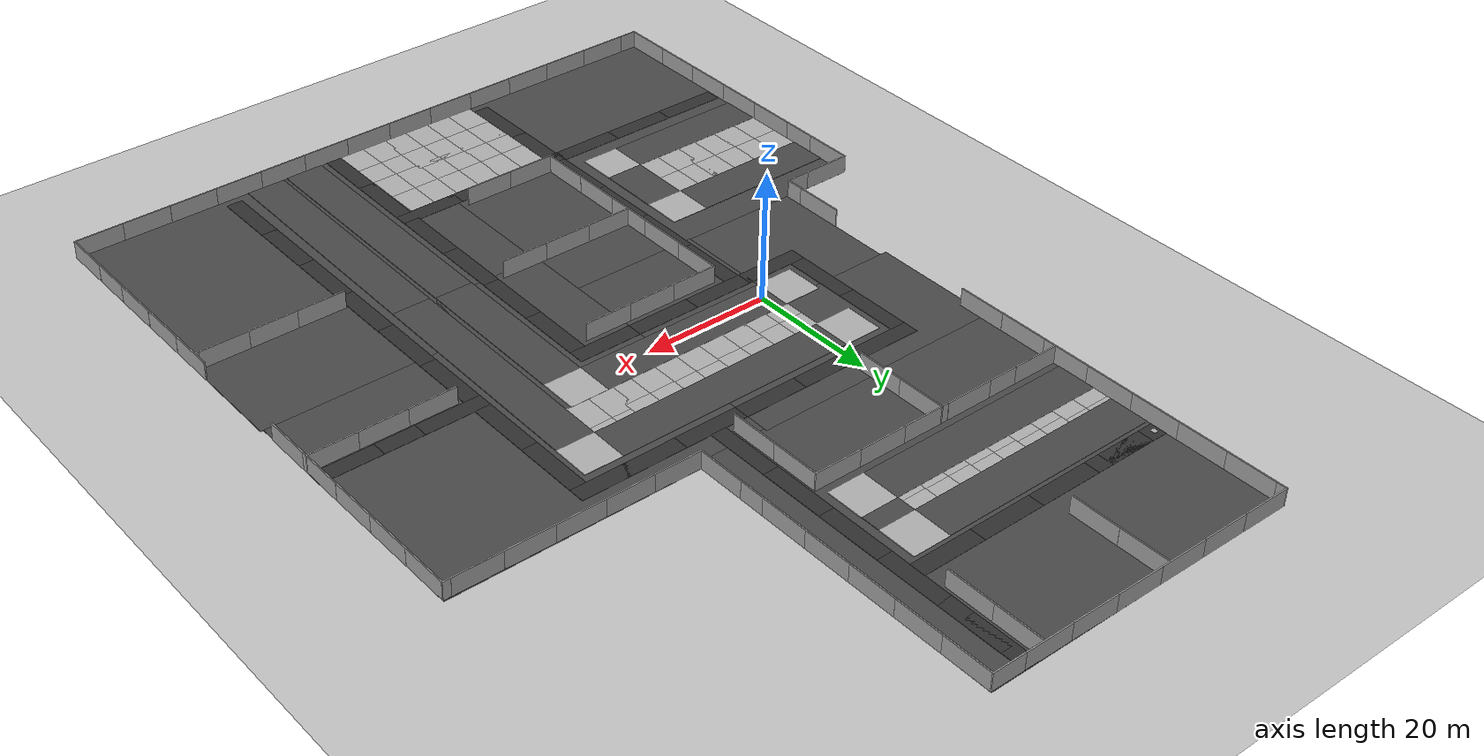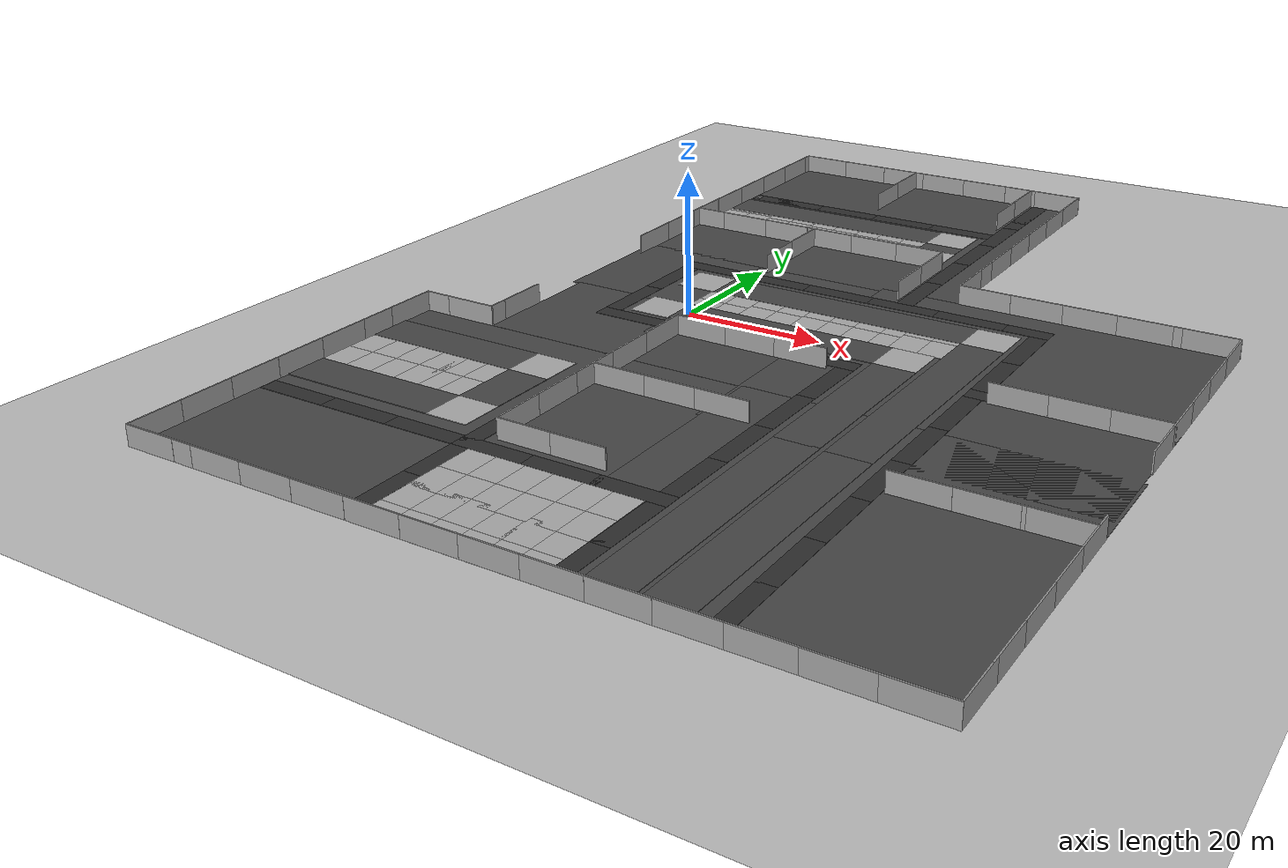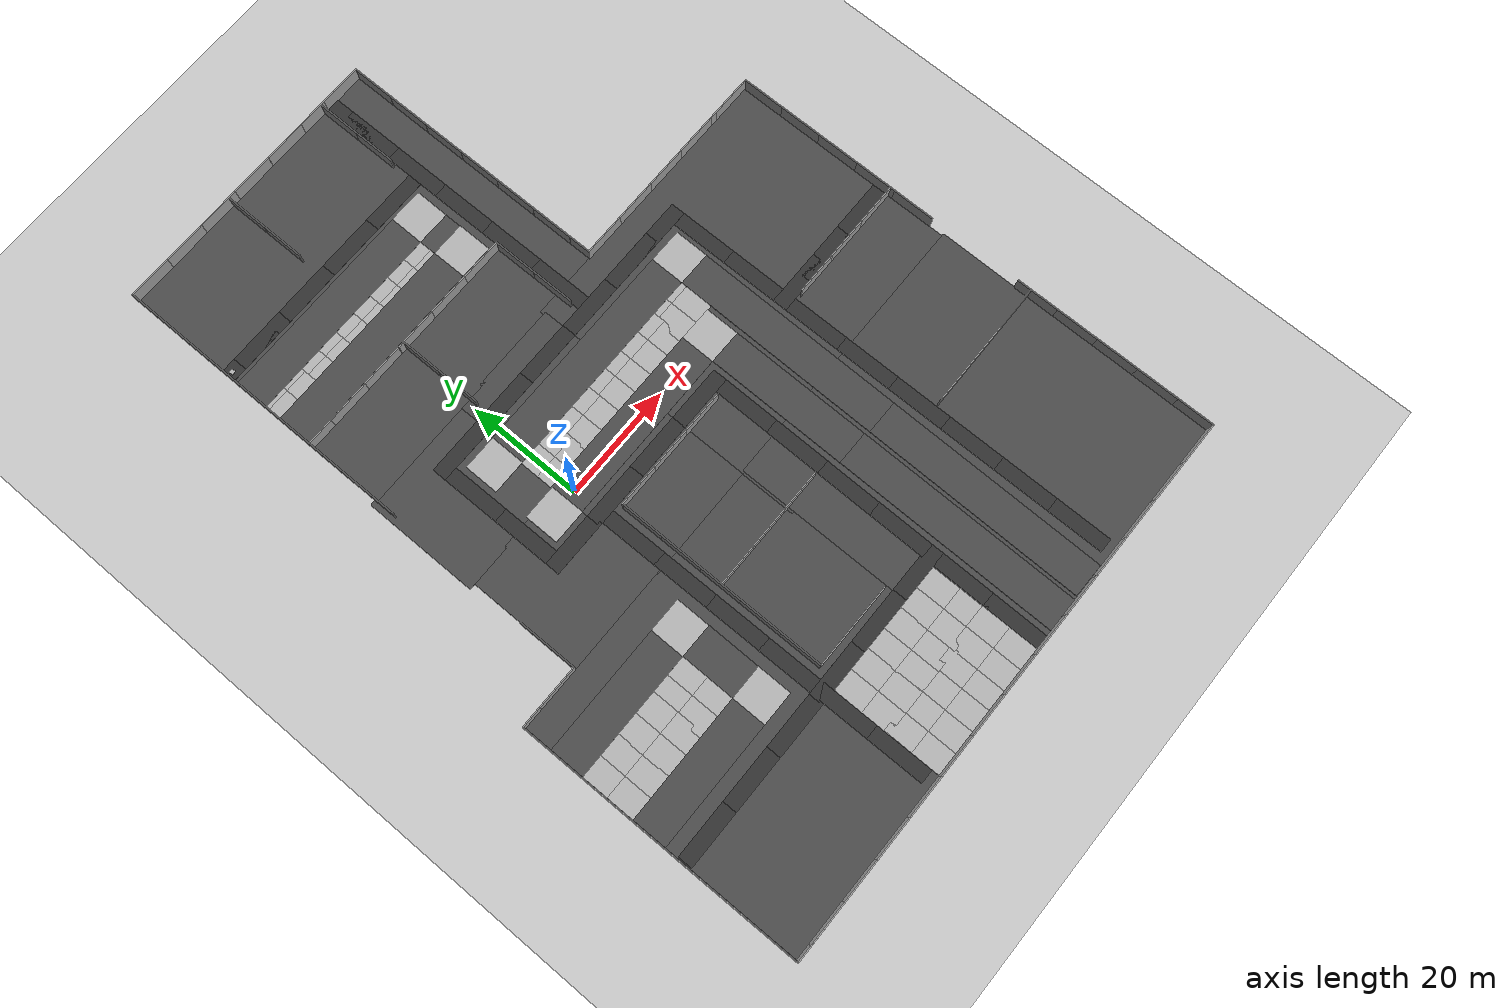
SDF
<sdf version="1.7">
 <world name="default">
  <plugin name="gazebo_ros_state" filename="libgazebo_ros_state.so">
   <ros>
    <namespace>/demo</namespace>
    <remapping>model_states:=model_states_demo</remapping>
    <remapping>link_states:=link_states_demo</remapping>
   </ros>
   <update_rate>1.0</update_rate>
  </plugin>
  <model name="ground_plane">
   <static>1</static>
   <link name="link">
    <collision name="collision">
     <geometry><plane><normal>0 0 1</normal><size>100 100</size></plane></geometry>
     <surface><friction><ode><mu>100</mu><mu2>50</mu2></ode></friction></surface>
    </collision>
    <visual name="visual">
     <cast_shadows>0</cast_shadows>
     <geometry><plane><normal>0 0 1</normal><size>100 100</size></plane></geometry>
     <material>
      <script><uri>file://media/materials/scripts/gazebo.material</uri><name>Gazebo/Grey</name></script>
     </material>
    </visual>
   </link>
  </model>
  <model name="asphalt_plane">
   <static>1</static>
   <link name="link">
    <collision name="collision">
     <geometry><box><size>20 20 0.1</size></box></geometry>
     <surface><friction><ode><mu>100</mu><mu2>50</mu2></ode></friction></surface>
    </collision>
    <visual name="visual">
     <cast_shadows>0</cast_shadows>
     <geometry><box><size>20 20 0.1</size></box></geometry>
     <material>
      <script>
       <uri>model://asphalt_plane/materials/scripts</uri>
       <uri>model://asphalt_plane/materials/textures</uri>
       <name>vrc/asphalt</name>
      </script>
     </material>
    </visual>
   </link>
   <pose>-10.1692 -7.43707 0 0 -0 0</pose>
  </model>
  <model name="asphalt_plane_clone">
   <static>1</static>
   <link name="link">
    <collision name="collision">
     <geometry><box><size>20 20 0.1</size></box></geometry>
     <surface><friction><ode><mu>100</mu><mu2>50</mu2></ode></friction></surface>
    </collision>
    <visual name="visual">
     <cast_shadows>0</cast_shadows>
     <geometry><box><size>20 20 0.1</size></box></geometry>
     <material>
      <script>
       <uri>model://asphalt_plane/materials/scripts</uri>
       <uri>model://asphalt_plane/materials/textures</uri>
       <name>vrc/asphalt</name>
      </script>
     </material>
    </visual>
   </link>
   <pose>-11.1971 12.1802 0 0 -0 0</pose>
  </model>
  <model name="asphalt_plane_clone_clone">
   <static>1</static>
   <link name="link">
    <collision name="collision">
     <geometry><box><size>20 20 0.1</size></box></geometry>
     <surface><friction><ode><mu>100</mu><mu2>50</mu2></ode></friction></surface>
    </collision>
    <visual name="visual">
     <cast_shadows>0</cast_shadows>
     <geometry><box><size>20 20 0.1</size></box></geometry>
     <material>
      <script>
       <uri>model://asphalt_plane/materials/scripts</uri>
       <uri>model://asphalt_plane/materials/textures</uri>
       <name>vrc/asphalt</name>
      </script>
     </material>
    </visual>
   </link>
   <pose>8.71597 12.1785 0 0 -0 0</pose>
  </model>
  <model name="asphalt_plane_clone_clone_0">
   <static>1</static>
   <link name="link">
    <collision name="collision">
     <geometry><box><size>20 20 0.1</size></box></geometry>
     <surface><friction><ode><mu>100</mu><mu2>50</mu2></ode></friction></surface>
    </collision>
    <visual name="visual">
     <cast_shadows>0</cast_shadows>
     <geometry><box><size>20 20 0.1</size></box></geometry>
     <material>
      <script>
       <uri>model://asphalt_plane/materials/scripts</uri>
       <uri>model://asphalt_plane/materials/textures</uri>
       <name>vrc/asphalt</name>
      </script>
     </material>
    </visual>
   </link>
   <pose>8.27987 -7.58982 0 0 -0 0</pose>
  </model>
  <model name="grey_wall_clone">
   <static>1</static>
   <link name="link">
    <pose>0 0 1.4 0 -0 0</pose>
    <collision name="collision"><geometry><box><size>7.5 0.2 2.8</size></box></geometry></collision>
    <visual name="visual">
     <cast_shadows>0</cast_shadows>
     <geometry><box><size>7.5 0.2 2.8</size></box></geometry>
     <material>
      <script>
       <uri>model://grey_wall/materials/scripts</uri>
       <uri>model://grey_wall/materials/textures</uri>
       <name>vrc/grey_wall</name>
      </script>
     </material>
    </visual>
   </link>
   <pose>49.4295 -33.5823 0 0 -0 0</pose>
  </model>
  <light name="sun" type="directional">
   <pose>0 0 10 0 -0 0</pose>
   <diffuse>0.8 0.8 0.8 1</diffuse>
   <specular>0.2 0.2 0.2 1</specular>
   <attenuation>
    <range>1000</range>
    <constant>0.9</constant>
    <linear>0.01</linear>
    <quadratic>0.001</quadratic>
   </attenuation>
   <direction>-0.5 0.1 -0.9</direction>
   <spot><inner_angle>0</inner_angle><outer_angle>0</outer_angle><falloff>0</falloff></spot>
  </light>
  <gravity>0 0 -9.8</gravity>
  <magnetic_field>6e-06 2.3e-05 -4.2e-05</magnetic_field>
  <atmosphere type="adiabatic"/>
  <physics name="default_physics" default="0" type="ode">
   <max_step_size>0.001</max_step_size>
   <real_time_factor>1</real_time_factor>
   <real_time_update_rate>1000</real_time_update_rate>
  </physics>
  <scene><ambient>0.4 0.4 0.4 1</ambient><background>0.7 0.7 0.7 1</background><shadows>0</shadows></scene>
  <audio><device>default</device></audio>
  <spherical_coordinates>
   <surface_model>EARTH_WGS84</surface_model>
   <latitude_deg>47.8406</latitude_deg>
   <longitude_deg>10.6199</longitude_deg>
   <elevation>740</elevation>
   <heading_deg>180</heading_deg>
  </spherical_coordinates>
  <model name="side walk">
   <pose>13.7924 17.3826 0 0 -0 0</pose>
   <static>1</static>
   <link name="link">
    <visual name="visual">
     <pose>0 0 0.05 0 -0 0</pose>
     <geometry><box><size>10 2.5 0.1</size></box></geometry>
     <material><ambient>0.2 0.2 0.2 1</ambient></material>
    </visual>
    <collision name="collision">
     <pose>0 0 0.05 0 -0 0</pose>
     <geometry><box><size>10 2.5 0.1</size></box></geometry>
    </collision>
   </link>
  </model>
  <model name="side walk_clone">
   <pose>3.79611 17.3771 0 0 -0 0</pose>
   <static>1</static>
   <link name="link">
    <visual name="visual">
     <pose>0 0 0.05 0 -0 0</pose>
     <geometry><box><size>10 2.5 0.1</size></box></geometry>
     <material><ambient>0.2 0.2 0.2 1</ambient></material>
    </visual>
    <collision name="collision">
     <pose>0 0 0.05 0 -0 0</pose>
     <geometry><box><size>10 2.5 0.1</size></box></geometry>
    </collision>
   </link>
  </model>
  <model name="side walk_clone_0">
   <pose>-6.19156 17.3637 0 0 -0 0</pose>
   <static>1</static>
   <link name="link">
    <visual name="visual">
     <pose>0 0 0.05 0 -0 0</pose>
     <geometry><box><size>10 2.5 0.1</size></box></geometry>
     <material><ambient>0.2 0.2 0.2 1</ambient></material>
    </visual>
    <collision name="collision">
     <pose>0 0 0.05 0 -0 0</pose>
     <geometry><box><size>10 2.5 0.1</size></box></geometry>
    </collision>
   </link>
  </model>
  <model name="side walk_clone_1">
   <pose>-9.91314 11.1641 0 0 0 -1.5667</pose>
   <static>1</static>
   <link name="link">
    <visual name="visual">
     <pose>0 0 0.05 0 -0 0</pose>
     <geometry><box><size>10 2.5 0.1</size></box></geometry>
     <material><ambient>0.2 0.2 0.2 1</ambient></material>
    </visual>
    <collision name="collision">
     <pose>0 0 0.05 0 -0 0</pose>
     <geometry><box><size>10 2.5 0.1</size></box></geometry>
    </collision>
   </link>
  </model>
  <model name="side walk_clone_1_clone">
   <pose>-9.88629 1.1782 0 0 0 -1.56946</pose>
   <static>1</static>
   <link name="link">
    <visual name="visual">
     <pose>0 0 0.05 0 -0 0</pose>
     <geometry><box><size>10 2.5 0.1</size></box></geometry>
     <material><ambient>0.2 0.2 0.2 1</ambient></material>
    </visual>
    <collision name="collision">
     <pose>0 0 0.05 0 -0 0</pose>
     <geometry><box><size>10 2.5 0.1</size></box></geometry>
    </collision>
   </link>
  </model>
  <model name="side walk_clone_0_clone">
   <pose>-6.1264 -5.0705 0 0 -0 0</pose>
   <static>1</static>
   <link name="link">
    <visual name="visual">
     <pose>0 0 0.05 0 -0 0</pose>
     <geometry><box><size>10 2.5 0.1</size></box></geometry>
     <material><ambient>0.2 0.2 0.2 1</ambient></material>
    </visual>
    <collision name="collision">
     <pose>0 0 0.05 0 -0 0</pose>
     <geometry><box><size>10 2.5 0.1</size></box></geometry>
    </collision>
   </link>
  </model>
  <model name="side walk_clone_0_clone_0">
   <pose>3.31852 -5.07088 0 0 -0 0</pose>
   <static>1</static>
   <link name="link">
    <visual name="visual">
     <pose>0 0 0.05 0 -0 0</pose>
     <geometry><box><size>10 2.5 0.1</size></box></geometry>
     <material><ambient>0.2 0.2 0.2 1</ambient></material>
    </visual>
    <collision name="collision">
     <pose>0 0 0.05 0 -0 0</pose>
     <geometry><box><size>10 2.5 0.1</size></box></geometry>
    </collision>
   </link>
  </model>
  <model name="side walk_clone_1_clone_clone">
   <pose>0.222815 -11.3123 0 0 0 -1.5667</pose>
   <static>1</static>
   <link name="link">
    <visual name="visual">
     <pose>0 0 0.05 0 -0 0</pose>
     <geometry><box><size>10 2.5 0.1</size></box></geometry>
     <material><ambient>0.2 0.2 0.2 1</ambient></material>
    </visual>
    <collision name="collision">
     <pose>0 0 0.05 0 -0 0</pose>
     <geometry><box><size>10 2.5 0.1</size></box></geometry>
    </collision>
   </link>
  </model>
  <model name="side walk_clone_0_clone_clone">
   <pose>13.2672 -5.07602 0 0 -0 0</pose>
   <static>1</static>
   <link name="link">
    <visual name="visual">
     <pose>0 0 0.05 0 -0 0</pose>
     <geometry><box><size>10 2.5 0.1</size></box></geometry>
     <material><ambient>0.2 0.2 0.2 1</ambient></material>
    </visual>
    <collision name="collision">
     <pose>0 0 0.05 0 -0 0</pose>
     <geometry><box><size>10 2.5 0.1</size></box></geometry>
    </collision>
   </link>
  </model>
  <model name="asphalt_plane_0">
   <static>1</static>
   <link name="link">
    <collision name="collision"><geometry><box><size>50 50 0.1</size></box></geometry></collision>
    <visual name="visual">
     <cast_shadows>0</cast_shadows>
     <geometry><box><size>50 50 0.1</size></box></geometry>
     <material>
      <script>
       <uri>model://asphalt_plane/materials/scripts</uri>
       <uri>model://asphalt_plane/materials/textures</uri>
       <name>vrc/asphalt</name>
      </script>
     </material>
    </visual>
   </link>
   <pose>-6.22709 -42.2685 -0.007309 0 -0 0</pose>
  </model>
  <model name="asphalt_plane_0_clone">
   <static>1</static>
   <link name="link">
    <collision name="collision"><geometry><box><size>50 50 0.1</size></box></geometry></collision>
    <visual name="visual">
     <cast_shadows>0</cast_shadows>
     <geometry><box><size>50 50 0.1</size></box></geometry>
     <material>
      <script>
       <uri>model://asphalt_plane/materials/scripts</uri>
       <uri>model://asphalt_plane/materials/textures</uri>
       <name>vrc/asphalt</name>
      </script>
     </material>
    </visual>
   </link>
   <pose>43.2053 -2.21198 0 0 -0 0</pose>
  </model>
  <model name="asphalt_plane_0_clone_clone">
   <static>1</static>
   <link name="link">
    <collision name="collision"><geometry><box><size>50 50 0.1</size></box></geometry></collision>
    <visual name="visual">
     <cast_shadows>0</cast_shadows>
     <geometry><box><size>50 50 0.1</size></box></geometry>
     <material>
      <script>
       <uri>model://asphalt_plane/materials/scripts</uri>
       <uri>model://asphalt_plane/materials/textures</uri>
       <name>vrc/asphalt</name>
      </script>
     </material>
    </visual>
   </link>
   <pose>4.81 46.7209 0 0 -0 0</pose>
  </model>
  <model name="side walk_clone_2">
   <pose>23.7417 17.3764 0 0 -0 0</pose>
   <static>1</static>
   <link name="link">
    <visual name="visual">
     <pose>0 0 0.05 0 -0 0</pose>
     <geometry><box><size>10 2.5 0.1</size></box></geometry>
     <material><ambient>0.2 0.2 0.2 1</ambient></material>
    </visual>
    <collision name="collision">
     <pose>0 0 0.05 0 -0 0</pose>
     <geometry><box><size>10 2.5 0.1</size></box></geometry>
    </collision>
   </link>
  </model>
  <model name="side walk_clone_3">
   <pose>33.7384 17.3743 0 0 -0 0</pose>
   <static>1</static>
   <link name="link">
    <visual name="visual">
     <pose>0 0 0.05 0 -0 0</pose>
     <geometry><box><size>10 2.5 0.1</size></box></geometry>
     <material><ambient>0.2 0.2 0.2 1</ambient></material>
    </visual>
    <collision name="collision">
     <pose>0 0 0.05 0 -0 0</pose>
     <geometry><box><size>10 2.5 0.1</size></box></geometry>
    </collision>
   </link>
  </model>
  <model name="side walk_clone_1_clone_clone_clone">
   <pose>23.5717 23.5135 0 0 0 -1.5667</pose>
   <static>1</static>
   <link name="link">
    <visual name="visual">
     <pose>0 0 0.05 0 -0 0</pose>
     <geometry><box><size>10 2.5 0.1</size></box></geometry>
     <material><ambient>0.2 0.2 0.2 1</ambient></material>
    </visual>
    <collision name="collision">
     <pose>0 0 0.05 0 -0 0</pose>
     <geometry><box><size>10 2.5 0.1</size></box></geometry>
    </collision>
   </link>
  </model>
  <model name="side walk_clone_1_clone_clone_clone_0">
   <pose>23.5407 33.4582 0 0 0 -1.5667</pose>
   <static>1</static>
   <link name="link">
    <visual name="visual">
     <pose>0 0 0.05 0 -0 0</pose>
     <geometry><box><size>10 2.5 0.1</size></box></geometry>
     <material><ambient>0.2 0.2 0.2 1</ambient></material>
    </visual>
    <collision name="collision">
     <pose>0 0 0.05 0 -0 0</pose>
     <geometry><box><size>10 2.5 0.1</size></box></geometry>
    </collision>
   </link>
  </model>
  <model name="side walk_clone_1_clone_clone_clone_1">
   <pose>23.5123 43.4347 0 0 0 -1.5667</pose>
   <static>1</static>
   <link name="link">
    <visual name="visual">
     <pose>0 0 0.05 0 -0 0</pose>
     <geometry><box><size>10 2.5 0.1</size></box></geometry>
     <material><ambient>0.2 0.2 0.2 1</ambient></material>
    </visual>
    <collision name="collision">
     <pose>0 0 0.05 0 -0 0</pose>
     <geometry><box><size>10 2.5 0.1</size></box></geometry>
    </collision>
   </link>
  </model>
  <model name="side walk_clone_1_clone_clone_clone_2">
   <pose>23.482 53.3149 0 0 0 -1.5667</pose>
   <static>1</static>
   <link name="link">
    <visual name="visual">
     <pose>0 0 0.05 0 -0 0</pose>
     <geometry><box><size>10 2.5 0.1</size></box></geometry>
     <material><ambient>0.2 0.2 0.2 1</ambient></material>
    </visual>
    <collision name="collision">
     <pose>0 0 0.05 0 -0 0</pose>
     <geometry><box><size>10 2.5 0.1</size></box></geometry>
    </collision>
   </link>
  </model>
  <model name="side walk_clone_1_clone_clone_clone_clone">
   <pose>0.256591 -21.2274 0 0 0 -1.5667</pose>
   <static>1</static>
   <link name="link">
    <visual name="visual">
     <pose>0 0 0.05 0 -0 0</pose>
     <geometry><box><size>10 2.5 0.1</size></box></geometry>
     <material><ambient>0.2 0.2 0.2 1</ambient></material>
    </visual>
    <collision name="collision">
     <pose>0 0 0.05 0 -0 0</pose>
     <geometry><box><size>10 2.5 0.1</size></box></geometry>
    </collision>
   </link>
  </model>
  <model name="side walk_clone_1_clone_clone_clone_clone_0">
   <pose>0.290651 -31.2092 0 0 0 -1.5667</pose>
   <static>1</static>
   <link name="link">
    <visual name="visual">
     <pose>0 0 0.05 0 -0 0</pose>
     <geometry><box><size>10 2.5 0.1</size></box></geometry>
     <material><ambient>0.2 0.2 0.2 1</ambient></material>
    </visual>
    <collision name="collision">
     <pose>0 0 0.05 0 -0 0</pose>
     <geometry><box><size>10 2.5 0.1</size></box></geometry>
    </collision>
   </link>
  </model>
  <model name="side walk_clone_0_clone_clone_clone">
   <pose>23.1677 -5.07058 0 0 -0 0</pose>
   <static>1</static>
   <link name="link">
    <visual name="visual">
     <pose>0 0 0.05 0 -0 0</pose>
     <geometry><box><size>10 2.5 0.1</size></box></geometry>
     <material><ambient>0.2 0.2 0.2 1</ambient></material>
    </visual>
    <collision name="collision">
     <pose>0 0 0.05 0 -0 0</pose>
     <geometry><box><size>10 2.5 0.1</size></box></geometry>
    </collision>
   </link>
  </model>
  <model name="side walk_clone_1_clone_clone_clone_clone_1">
   <pose>43.9499 11.1428 0 0 0 -1.5667</pose>
   <static>1</static>
   <link name="link">
    <visual name="visual">
     <pose>0 0 0.05 0 -0 0</pose>
     <geometry><box><size>10 2.5 0.1</size></box></geometry>
     <material><ambient>0.2 0.2 0.2 1</ambient></material>
    </visual>
    <collision name="collision">
     <pose>0 0 0.05 0 -0 0</pose>
     <geometry><box><size>10 2.5 0.1</size></box></geometry>
    </collision>
   </link>
  </model>
  <model name="side walk_clone_1_clone_clone_clone_clone_2">
   <pose>43.9881 1.1868 0 0 0 -1.5667</pose>
   <static>1</static>
   <link name="link">
    <visual name="visual">
     <pose>0 0 0.05 0 -0 0</pose>
     <geometry><box><size>10 2.5 0.1</size></box></geometry>
     <material><ambient>0.2 0.2 0.2 1</ambient></material>
    </visual>
    <collision name="collision">
     <pose>0 0 0.05 0 -0 0</pose>
     <geometry><box><size>10 2.5 0.1</size></box></geometry>
    </collision>
   </link>
  </model>
  <model name="side walk_clone_0_clone_clone_clone_0_clone_clone">
   <pose>53.9006 -4.98965 0 0 -0 0</pose>
   <static>1</static>
   <link name="link">
    <visual name="visual">
     <pose>0 0 0.05 0 -0 0</pose>
     <geometry><box><size>10 2.5 0.1</size></box></geometry>
     <material><ambient>0.2 0.2 0.2 1</ambient></material>
    </visual>
    <collision name="collision">
     <pose>0 0 0.05 0 -0 0</pose>
     <geometry><box><size>10 2.5 0.1</size></box></geometry>
    </collision>
   </link>
  </model>
  <model name="side walk_clone_0_clone_clone_clone_0_clone_clone_0">
   <pose>63.3362 -4.96787 0 0 -0 0</pose>
   <static>1</static>
   <link name="link">
    <visual name="visual">
     <pose>0 0 0.05 0 -0 0</pose>
     <geometry><box><size>10 2.5 0.1</size></box></geometry>
     <material><ambient>0.2 0.2 0.2 1</ambient></material>
    </visual>
    <collision name="collision">
     <pose>0 0 0.05 0 -0 0</pose>
     <geometry><box><size>10 2.5 0.1</size></box></geometry>
    </collision>
   </link>
  </model>
  <model name="side walk_clone_1_clone_clone_clone_2_clone">
   <pose>23.4414 63.1752 0 0 0 -1.5667</pose>
   <static>1</static>
   <link name="link">
    <visual name="visual">
     <pose>0 0 0.05 0 -0 0</pose>
     <geometry><box><size>10 2.5 0.1</size></box></geometry>
     <material><ambient>0.2 0.2 0.2 1</ambient></material>
    </visual>
    <collision name="collision">
     <pose>0 0 0.05 0 -0 0</pose>
     <geometry><box><size>10 2.5 0.1</size></box></geometry>
    </collision>
   </link>
  </model>
  <model name="side walk_clone_1_clone_clone_clone_2_clone_0">
   <pose>23.4031 66.7362 0 0 0 -1.5667</pose>
   <static>1</static>
   <link name="link">
    <visual name="visual">
     <pose>0 0 0.05 0 -0 0</pose>
     <geometry><box><size>10 2.5 0.1</size></box></geometry>
     <material><ambient>0.2 0.2 0.2 1</ambient></material>
    </visual>
    <collision name="collision">
     <pose>0 0 0.05 0 -0 0</pose>
     <geometry><box><size>10 2.5 0.1</size></box></geometry>
    </collision>
   </link>
  </model>
  <model name="grey_wall_clone_clone">
   <static>1</static>
   <link name="link">
    <pose>0 0 1.4 0 -0 0</pose>
    <collision name="collision"><geometry><box><size>7.5 0.2 2.8</size></box></geometry></collision>
    <visual name="visual">
     <cast_shadows>0</cast_shadows>
     <geometry><box><size>7.5 0.2 2.8</size></box></geometry>
     <material>
      <script>
       <uri>model://grey_wall/materials/scripts</uri>
       <uri>model://grey_wall/materials/textures</uri>
       <name>vrc/grey_wall</name>
      </script>
     </material>
    </visual>
   </link>
   <pose>0.663264 23.7766 0 0 0 -1.56776</pose>
  </model>
  <model name="side walk_clone_4_clone">
   <pose>17.2612 52.615 0 0 -0 0</pose>
   <static>1</static>
   <link name="link">
    <visual name="visual">
     <pose>0 0 0.05 0 -0 0</pose>
     <geometry><box><size>10 2.5 0.1</size></box></geometry>
     <material><ambient>0.2 0.2 0.2 1</ambient></material>
    </visual>
    <collision name="collision">
     <pose>0 0 0.05 0 -0 0</pose>
     <geometry><box><size>10 2.5 0.1</size></box></geometry>
    </collision>
   </link>
  </model>
  <model name="side walk_clone_4_clone_0">
   <pose>7.25478 52.6157 0 0 -0 0</pose>
   <static>1</static>
   <link name="link">
    <visual name="visual">
     <pose>0 0 0.05 0 -0 0</pose>
     <geometry><box><size>10 2.5 0.1</size></box></geometry>
     <material><ambient>0.2 0.2 0.2 1</ambient></material>
    </visual>
    <collision name="collision">
     <pose>0 0 0.05 0 -0 0</pose>
     <geometry><box><size>10 2.5 0.1</size></box></geometry>
    </collision>
   </link>
  </model>
  <model name="side walk_clone_4_clone_1">
   <pose>-2.73893 52.607 0 0 -0 0</pose>
   <static>1</static>
   <link name="link">
    <visual name="visual">
     <pose>0 0 0.05 0 -0 0</pose>
     <geometry><box><size>10 2.5 0.1</size></box></geometry>
     <material><ambient>0.2 0.2 0.2 1</ambient></material>
    </visual>
    <collision name="collision">
     <pose>0 0 0.05 0 -0 0</pose>
     <geometry><box><size>10 2.5 0.1</size></box></geometry>
    </collision>
   </link>
  </model>
  <model name="side walk_clone_4_clone_2">
   <pose>-12.7156 52.6002 0 0 -0 0</pose>
   <static>1</static>
   <link name="link">
    <visual name="visual">
     <pose>0 0 0.05 0 -0 0</pose>
     <geometry><box><size>10 2.5 0.1</size></box></geometry>
     <material><ambient>0.2 0.2 0.2 1</ambient></material>
    </visual>
    <collision name="collision">
     <pose>0 0 0.05 0 -0 0</pose>
     <geometry><box><size>10 2.5 0.1</size></box></geometry>
    </collision>
   </link>
  </model>
  <model name="grey_wall_clone_clone_clone">
   <static>1</static>
   <link name="link">
    <pose>0 0 1.4 0 -0 0</pose>
    <collision name="collision"><geometry><box><size>7.5 0.2 2.8</size></box></geometry></collision>
    <visual name="visual">
     <cast_shadows>0</cast_shadows>
     <geometry><box><size>7.5 0.2 2.8</size></box></geometry>
     <material>
      <script>
       <uri>model://grey_wall/materials/scripts</uri>
       <uri>model://grey_wall/materials/textures</uri>
       <name>vrc/grey_wall</name>
      </script>
     </material>
    </visual>
   </link>
   <pose>0.641842 31.1008 0 0 0 -1.56776</pose>
  </model>
  <model name="grey_wall_clone_clone_clone_0">
   <static>1</static>
   <link name="link">
    <pose>0 0 1.4 0 -0 0</pose>
    <collision name="collision"><geometry><box><size>7.5 0.2 2.8</size></box></geometry></collision>
    <visual name="visual">
     <cast_shadows>0</cast_shadows>
     <geometry><box><size>7.5 0.2 2.8</size></box></geometry>
     <material>
      <script>
       <uri>model://grey_wall/materials/scripts</uri>
       <uri>model://grey_wall/materials/textures</uri>
       <name>vrc/grey_wall</name>
      </script>
     </material>
    </visual>
   </link>
   <pose>0.782654 60.3851 0 0 0 -1.56776</pose>
  </model>
  <model name="grey_wall_clone_clone_clone_1">
   <static>1</static>
   <link name="link">
    <pose>0 0 1.4 0 -0 0</pose>
    <collision name="collision"><geometry><box><size>7.5 0.2 2.8</size></box></geometry></collision>
    <visual name="visual">
     <cast_shadows>0</cast_shadows>
     <geometry><box><size>7.5 0.2 2.8</size></box></geometry>
     <material>
      <script>
       <uri>model://grey_wall/materials/scripts</uri>
       <uri>model://grey_wall/materials/textures</uri>
       <name>vrc/grey_wall</name>
      </script>
     </material>
    </visual>
   </link>
   <pose>0.745884 67.8409 0 0 0 -1.56776</pose>
  </model>
  <model name="grey_wall_clone_clone_clone_2">
   <static>1</static>
   <link name="link">
    <pose>0 0 1.4 0 -0 0</pose>
    <collision name="collision"><geometry><box><size>7.5 0.2 2.8</size></box></geometry></collision>
    <visual name="visual">
     <cast_shadows>0</cast_shadows>
     <geometry><box><size>7.5 0.2 2.8</size></box></geometry>
     <material>
      <script>
       <uri>model://grey_wall/materials/scripts</uri>
       <uri>model://grey_wall/materials/textures</uri>
       <name>vrc/grey_wall</name>
      </script>
     </material>
    </visual>
   </link>
   <pose>-4.2983 34.7434 0 0 -0 3.13795</pose>
  </model>
  <model name="grey_wall_clone_clone_clone_2_clone">
   <static>1</static>
   <link name="link">
    <pose>0 0 1.4 0 -0 0</pose>
    <collision name="collision"><geometry><box><size>7.5 0.2 2.8</size></box></geometry></collision>
    <visual name="visual">
     <cast_shadows>0</cast_shadows>
     <geometry><box><size>7.5 0.2 2.8</size></box></geometry>
     <material>
      <script>
       <uri>model://grey_wall/materials/scripts</uri>
       <uri>model://grey_wall/materials/textures</uri>
       <name>vrc/grey_wall</name>
      </script>
     </material>
    </visual>
   </link>
   <pose>-11.7464 34.7461 0 0 -0 3.13795</pose>
  </model>
  <model name="grey_wall_clone_clone_clone_2_clone_0">
   <static>1</static>
   <link name="link">
    <pose>0 0 1.4 0 -0 0</pose>
    <collision name="collision"><geometry><box><size>7.5 0.2 2.8</size></box></geometry></collision>
    <visual name="visual">
     <cast_shadows>0</cast_shadows>
     <geometry><box><size>7.5 0.2 2.8</size></box></geometry>
     <material>
      <script>
       <uri>model://grey_wall/materials/scripts</uri>
       <uri>model://grey_wall/materials/textures</uri>
       <name>vrc/grey_wall</name>
      </script>
     </material>
    </visual>
   </link>
   <pose>-16.4804 34.7656 0 0 -0 3.13795</pose>
  </model>
  <model name="grey_wall_clone_clone_clone_2_clone_1">
   <static>1</static>
   <link name="link">
    <pose>0 0 1.4 0 -0 0</pose>
    <collision name="collision"><geometry><box><size>7.5 0.2 2.8</size></box></geometry></collision>
    <visual name="visual">
     <cast_shadows>0</cast_shadows>
     <geometry><box><size>7.5 0.2 2.8</size></box></geometry>
     <material>
      <script>
       <uri>model://grey_wall/materials/scripts</uri>
       <uri>model://grey_wall/materials/textures</uri>
       <name>vrc/grey_wall</name>
      </script>
     </material>
    </visual>
   </link>
   <pose>3.28789 34.7184 0 0 -0 3.13795</pose>
  </model>
  <model name="grey_wall_clone_clone_clone_2_clone_2">
   <static>1</static>
   <link name="link">
    <pose>0 0 1.4 0 -0 0</pose>
    <collision name="collision"><geometry><box><size>7.5 0.2 2.8</size></box></geometry></collision>
    <visual name="visual">
     <cast_shadows>0</cast_shadows>
     <geometry><box><size>7.5 0.2 2.8</size></box></geometry>
     <material>
      <script>
       <uri>model://grey_wall/materials/scripts</uri>
       <uri>model://grey_wall/materials/textures</uri>
       <name>vrc/grey_wall</name>
      </script>
     </material>
    </visual>
   </link>
   <pose>10.7527 34.6951 0 0 -0 3.13795</pose>
  </model>
  <model name="grey_wall_clone_clone_clone_2_clone_3">
   <static>1</static>
   <link name="link">
    <pose>0 0 1.4 0 -0 0</pose>
    <collision name="collision"><geometry><box><size>7.5 0.2 2.8</size></box></geometry></collision>
    <visual name="visual">
     <cast_shadows>0</cast_shadows>
     <geometry><box><size>7.5 0.2 2.8</size></box></geometry>
     <material>
      <script>
       <uri>model://grey_wall/materials/scripts</uri>
       <uri>model://grey_wall/materials/textures</uri>
       <name>vrc/grey_wall</name>
      </script>
     </material>
    </visual>
   </link>
   <pose>18.2492 34.6563 0 0 -0 3.13795</pose>
  </model>
  <model name="grey_wall_clone_clone_clone_clone">
   <static>1</static>
   <link name="link">
    <pose>0 0 1.4 0 -0 0</pose>
    <collision name="collision"><geometry><box><size>7.5 0.2 2.8</size></box></geometry></collision>
    <visual name="visual">
     <cast_shadows>0</cast_shadows>
     <geometry><box><size>7.5 0.2 2.8</size></box></geometry>
     <material>
      <script>
       <uri>model://grey_wall/materials/scripts</uri>
       <uri>model://grey_wall/materials/textures</uri>
       <name>vrc/grey_wall</name>
      </script>
     </material>
    </visual>
   </link>
   <pose>21.9008 30.8248 0 0 0 -1.56776</pose>
  </model>
  <model name="grey_wall_clone_clone_clone_clone_0">
   <static>1</static>
   <link name="link">
    <pose>0 0 1.4 0 -0 0</pose>
    <collision name="collision"><geometry><box><size>7.5 0.2 2.8</size></box></geometry></collision>
    <visual name="visual">
     <cast_shadows>0</cast_shadows>
     <geometry><box><size>7.5 0.2 2.8</size></box></geometry>
     <material>
      <script>
       <uri>model://grey_wall/materials/scripts</uri>
       <uri>model://grey_wall/materials/textures</uri>
       <name>vrc/grey_wall</name>
      </script>
     </material>
    </visual>
   </link>
   <pose>21.932 23.3788 0 0 0 -1.56776</pose>
  </model>
  <model name="grey_wall_clone_clone_clone_2_clone_0_clone">
   <static>1</static>
   <link name="link">
    <pose>0 0 1.4 0 -0 0</pose>
    <collision name="collision"><geometry><box><size>7.5 0.2 2.8</size></box></geometry></collision>
    <visual name="visual">
     <cast_shadows>0</cast_shadows>
     <geometry><box><size>7.5 0.2 2.8</size></box></geometry>
     <material>
      <script>
       <uri>model://grey_wall/materials/scripts</uri>
       <uri>model://grey_wall/materials/textures</uri>
       <name>vrc/grey_wall</name>
      </script>
     </material>
    </visual>
   </link>
   <pose>-16.4775 71.7397 0 0 -0 3.13795</pose>
  </model>
  <model name="grey_wall_clone_clone_clone_2_clone_0_clone_0">
   <static>1</static>
   <link name="link">
    <pose>0 0 1.4 0 -0 0</pose>
    <collision name="collision"><geometry><box><size>7.5 0.2 2.8</size></box></geometry></collision>
    <visual name="visual">
     <cast_shadows>0</cast_shadows>
     <geometry><box><size>7.5 0.2 2.8</size></box></geometry>
     <material>
      <script>
       <uri>model://grey_wall/materials/scripts</uri>
       <uri>model://grey_wall/materials/textures</uri>
       <name>vrc/grey_wall</name>
      </script>
     </material>
    </visual>
   </link>
   <pose>-9.07049 71.7023 0 0 -0 3.13795</pose>
  </model>
  <model name="grey_wall_clone_clone_clone_2_clone_0_clone_1">
   <static>1</static>
   <link name="link">
    <pose>0 0 1.4 0 -0 0</pose>
    <collision name="collision"><geometry><box><size>7.5 0.2 2.8</size></box></geometry></collision>
    <visual name="visual">
     <cast_shadows>0</cast_shadows>
     <geometry><box><size>7.5 0.2 2.8</size></box></geometry>
     <material>
      <script>
       <uri>model://grey_wall/materials/scripts</uri>
       <uri>model://grey_wall/materials/textures</uri>
       <name>vrc/grey_wall</name>
      </script>
     </material>
    </visual>
   </link>
   <pose>-1.64416 71.6785 0 0 -0 3.13795</pose>
  </model>
  <model name="grey_wall_clone_clone_clone_2_clone_0_clone_2">
   <static>1</static>
   <link name="link">
    <pose>0 0 1.4 0 -0 0</pose>
    <collision name="collision"><geometry><box><size>7.5 0.2 2.8</size></box></geometry></collision>
    <visual name="visual">
     <cast_shadows>0</cast_shadows>
     <geometry><box><size>7.5 0.2 2.8</size></box></geometry>
     <material>
      <script>
       <uri>model://grey_wall/materials/scripts</uri>
       <uri>model://grey_wall/materials/textures</uri>
       <name>vrc/grey_wall</name>
      </script>
     </material>
    </visual>
   </link>
   <pose>5.83626 71.649 0 0 -0 3.13795</pose>
  </model>
  <model name="grey_wall_clone_clone_clone_2_clone_0_clone_3">
   <static>1</static>
   <link name="link">
    <pose>0 0 1.4 0 -0 0</pose>
    <collision name="collision"><geometry><box><size>7.5 0.2 2.8</size></box></geometry></collision>
    <visual name="visual">
     <cast_shadows>0</cast_shadows>
     <geometry><box><size>7.5 0.2 2.8</size></box></geometry>
     <material>
      <script>
       <uri>model://grey_wall/materials/scripts</uri>
       <uri>model://grey_wall/materials/textures</uri>
       <name>vrc/grey_wall</name>
      </script>
     </material>
    </visual>
   </link>
   <pose>13.3382 71.616 0 0 -0 3.13795</pose>
  </model>
  <model name="grey_wall_clone_clone_clone_2_clone_0_clone_4">
   <static>1</static>
   <link name="link">
    <pose>0 0 1.4 0 -0 0</pose>
    <collision name="collision"><geometry><box><size>7.5 0.2 2.8</size></box></geometry></collision>
    <visual name="visual">
     <cast_shadows>0</cast_shadows>
     <geometry><box><size>7.5 0.2 2.8</size></box></geometry>
     <material>
      <script>
       <uri>model://grey_wall/materials/scripts</uri>
       <uri>model://grey_wall/materials/textures</uri>
       <name>vrc/grey_wall</name>
      </script>
     </material>
    </visual>
   </link>
   <pose>20.8292 71.5956 0 0 -0 3.13795</pose>
  </model>
  <model name="grey_wall_clone_clone_clone_2_clone_0_clone_5">
   <static>1</static>
   <link name="link">
    <pose>0 0 1.4 0 -0 0</pose>
    <collision name="collision"><geometry><box><size>7.5 0.2 2.8</size></box></geometry></collision>
    <visual name="visual">
     <cast_shadows>0</cast_shadows>
     <geometry><box><size>7.5 0.2 2.8</size></box></geometry>
     <material>
      <script>
       <uri>model://grey_wall/materials/scripts</uri>
       <uri>model://grey_wall/materials/textures</uri>
       <name>vrc/grey_wall</name>
      </script>
     </material>
    </visual>
   </link>
   <pose>26.0628 71.555 0 0 -0 3.13795</pose>
  </model>
  <model name="side walk_clone_0_clone_clone_clone_0_clone_clone_3">
   <pose>3.83426 -46.9929 0 0 -0 0</pose>
   <static>1</static>
   <link name="link">
    <visual name="visual">
     <pose>0 0 0.05 0 -0 0</pose>
     <geometry><box><size>10 2.5 0.1</size></box></geometry>
     <material><ambient>0.2 0.2 0.2 1</ambient></material>
    </visual>
    <collision name="collision">
     <pose>0 0 0.05 0 -0 0</pose>
     <geometry><box><size>10 2.5 0.1</size></box></geometry>
    </collision>
   </link>
  </model>
  <model name="side walk_clone_0_clone_clone_clone_0_clone_clone_4">
   <pose>-5.93815 -47.0144 0 0 -0 0</pose>
   <static>1</static>
   <link name="link">
    <visual name="visual">
     <pose>0 0 0.05 0 -0 0</pose>
     <geometry><box><size>10 2.5 0.1</size></box></geometry>
     <material><ambient>0.2 0.2 0.2 1</ambient></material>
    </visual>
    <collision name="collision">
     <pose>0 0 0.05 0 -0 0</pose>
     <geometry><box><size>10 2.5 0.1</size></box></geometry>
    </collision>
   </link>
  </model>
  <model name="side walk_clone_0_clone_clone_clone_0_clone_clone_5">
   <pose>-15.9248 -47.0111 0 0 -0 0</pose>
   <static>1</static>
   <link name="link">
    <visual name="visual">
     <pose>0 0 0.05 0 -0 0</pose>
     <geometry><box><size>10 2.5 0.1</size></box></geometry>
     <material><ambient>0.2 0.2 0.2 1</ambient></material>
    </visual>
    <collision name="collision">
     <pose>0 0 0.05 0 -0 0</pose>
     <geometry><box><size>10 2.5 0.1</size></box></geometry>
    </collision>
   </link>
  </model>
  <model name="side walk_clone_0_clone_clone_clone_0_clone_clone_6">
   <pose>-25.9206 -47.0184 0 0 -0 0</pose>
   <static>1</static>
   <link name="link">
    <visual name="visual">
     <pose>0 0 0.05 0 -0 0</pose>
     <geometry><box><size>10 2.5 0.1</size></box></geometry>
     <material><ambient>0.2 0.2 0.2 1</ambient></material>
    </visual>
    <collision name="collision">
     <pose>0 0 0.05 0 -0 0</pose>
     <geometry><box><size>10 2.5 0.1</size></box></geometry>
    </collision>
   </link>
  </model>
  <model name="side walk_clone_0_clone_clone_clone_0_clone_clone_7">
   <pose>13.792 -46.9837 0 0 -0 0</pose>
   <static>1</static>
   <link name="link">
    <visual name="visual">
     <pose>0 0 0.05 0 -0 0</pose>
     <geometry><box><size>10 2.5 0.1</size></box></geometry>
     <material><ambient>0.2 0.2 0.2 1</ambient></material>
    </visual>
    <collision name="collision">
     <pose>0 0 0.05 0 -0 0</pose>
     <geometry><box><size>10 2.5 0.1</size></box></geometry>
    </collision>
   </link>
  </model>
  <model name="side walk_clone_1_clone_clone_clone_clone_0_clone">
   <pose>0.312658 -41.1369 0 0 0 -1.5667</pose>
   <static>1</static>
   <link name="link">
    <visual name="visual">
     <pose>0 0 0.05 0 -0 0</pose>
     <geometry><box><size>10 2.5 0.1</size></box></geometry>
     <material><ambient>0.2 0.2 0.2 1</ambient></material>
    </visual>
    <collision name="collision">
     <pose>0 0 0.05 0 -0 0</pose>
     <geometry><box><size>10 2.5 0.1</size></box></geometry>
    </collision>
   </link>
  </model>
  <model name="side walk_clone_1_clone_clone_clone_clone_0_clone_0">
   <pose>0.356942 -51.0999 0 0 0 -1.5667</pose>
   <static>1</static>
   <link name="link">
    <visual name="visual">
     <pose>0 0 0.05 0 -0 0</pose>
     <geometry><box><size>10 2.5 0.1</size></box></geometry>
     <material><ambient>0.2 0.2 0.2 1</ambient></material>
    </visual>
    <collision name="collision">
     <pose>0 0 0.05 0 -0 0</pose>
     <geometry><box><size>10 2.5 0.1</size></box></geometry>
    </collision>
   </link>
  </model>
  <model name="side walk_clone_1_clone_clone_clone_clone_0_clone_0_clone">
   <pose>0.402208 -61.0372 0 0 0 -1.5667</pose>
   <static>1</static>
   <link name="link">
    <visual name="visual">
     <pose>0 0 0.05 0 -0 0</pose>
     <geometry><box><size>10 2.5 0.1</size></box></geometry>
     <material><ambient>0.2 0.2 0.2 1</ambient></material>
    </visual>
    <collision name="collision">
     <pose>0 0 0.05 0 -0 0</pose>
     <geometry><box><size>10 2.5 0.1</size></box></geometry>
    </collision>
   </link>
  </model>
  <model name="mud_box_clone_5">
   <static>1</static>
   <link name="link">
    <collision name="collision"><geometry><box><size>8 10 0.2</size></box></geometry></collision>
    <visual name="visual_1">
     <pose>-2 2.5 0 0 -0 0</pose>
     <cast_shadows>0</cast_shadows>
     <geometry><box><size>4 5 0.2</size></box></geometry>
     <material>
      <script>
       <uri>model://mud_box/materials/scripts</uri>
       <uri>model://mud_box/materials/textures</uri>
       <name>vrc/mud</name>
      </script>
     </material>
    </visual>
    <visual name="visual_2">
     <pose>2 2.5 0 0 -0 0</pose>
     <cast_shadows>0</cast_shadows>
     <geometry><box><size>4 5 0.2</size></box></geometry>
     <material>
      <script>
       <uri>model://mud_box/materials/scripts</uri>
       <uri>model://mud_box/materials/textures</uri>
       <name>vrc/mud</name>
      </script>
     </material>
    </visual>
    <visual name="visual_3">
     <pose>2 -2.5 0 0 -0 0</pose>
     <cast_shadows>0</cast_shadows>
     <geometry><box><size>4 5 0.2</size></box></geometry>
     <material>
      <script>
       <uri>model://mud_box/materials/scripts</uri>
       <uri>model://mud_box/materials/textures</uri>
       <name>vrc/mud</name>
      </script>
     </material>
    </visual>
    <visual name="visual_4">
     <pose>-2 -2.5 0 0 -0 0</pose>
     <cast_shadows>0</cast_shadows>
     <geometry><box><size>4 5 0.2</size></box></geometry>
     <material>
      <script>
       <uri>model://mud_box/materials/scripts</uri>
       <uri>model://mud_box/materials/textures</uri>
       <name>vrc/mud</name>
      </script>
     </material>
    </visual>
   </link>
   <pose>5.61442 -53.24 0 0 -0 0</pose>
  </model>
  <model name="road_plane_without_marks">
   <static>1</static>
   <link name="link">
    <collision name="collision"><geometry><box><size>22.5097 6 0.1</size></box></geometry></collision>
    <visual name="visual">
     <cast_shadows>0</cast_shadows>
     <geometry><box><size>22.5097 6 0.1</size></box></geometry>
     <material>
      <script>
       <uri>model://road_plane_without_marks/materials/scripts</uri>
       <uri>model://road_plane_without_marks/materials/textures</uri>
       <name>vrc/road_no_m</name>
      </script>
     </material>
    </visual>
   </link>
   <pose>-19.9337 -40.6069 0.081661 0 -0 0</pose>
  </model>
  <model name="road_diag">
   <static>1</static>
   <link name="link">
    <collision name="collision"><geometry><box><size>6 6 0.1</size></box></geometry></collision>
    <visual name="visual">
     <cast_shadows>0</cast_shadows>
     <geometry><box><size>6 6 0.1</size></box></geometry>
     <material>
      <script>
       <uri>model://road_diag/materials/scripts</uri>
       <uri>model://road_diag/materials/textures</uri>
       <name>vrc/diag</name>
      </script>
     </material>
    </visual>
   </link>
   <pose>-5.72976 -40.6178 0.084251 0 -0 0</pose>
  </model>
  <model name="road_plane_without_marks_clone">
   <static>1</static>
   <link name="link">
    <collision name="collision"><geometry><box><size>22.5097 6 0.1</size></box></geometry></collision>
    <visual name="visual">
     <cast_shadows>0</cast_shadows>
     <geometry><box><size>22.5097 6 0.1</size></box></geometry>
     <material>
      <script>
       <uri>model://road_plane_without_marks/materials/scripts</uri>
       <uri>model://road_plane_without_marks/materials/textures</uri>
       <name>vrc/road_no_m</name>
      </script>
     </material>
    </visual>
   </link>
   <pose>-19.9247 -25.2286 0.081661 0 -0 0</pose>
  </model>
  <model name="road_diag_clone">
   <static>1</static>
   <link name="link">
    <collision name="collision"><geometry><box><size>6 6 0.1</size></box></geometry></collision>
    <visual name="visual">
     <cast_shadows>0</cast_shadows>
     <geometry><box><size>6 6 0.1</size></box></geometry>
     <material>
      <script>
       <uri>model://road_diag/materials/scripts</uri>
       <uri>model://road_diag/materials/textures</uri>
       <name>vrc/diag</name>
      </script>
     </material>
    </visual>
   </link>
   <pose>-5.71886 -25.2377 0.084251 0 -0 1.56496</pose>
  </model>
  <model name="road_plane_without_marks_clone_0">
   <static>1</static>
   <link name="link">
    <collision name="collision"><geometry><box><size>9.63712 6 0.1</size></box></geometry></collision>
    <visual name="visual">
     <cast_shadows>0</cast_shadows>
     <geometry><box><size>9.63712 6 0.1</size></box></geometry>
     <material>
      <script>
       <uri>model://road_plane_without_marks/materials/scripts</uri>
       <uri>model://road_plane_without_marks/materials/textures</uri>
       <name>vrc/road_no_m</name>
      </script>
     </material>
    </visual>
   </link>
   <pose>-5.71284 -32.9976 0.081661 0 -0 1.56522</pose>
  </model>
  <model name="road_plane_without_marks_clone_clone">
   <static>1</static>
   <link name="link">
    <collision name="collision"><geometry><box><size>37.9662 6 0.1</size></box></geometry></collision>
    <visual name="visual">
     <cast_shadows>0</cast_shadows>
     <geometry><box><size>37.9662 6 0.1</size></box></geometry>
     <material>
      <script>
       <uri>model://road_plane_without_marks/materials/scripts</uri>
       <uri>model://road_plane_without_marks/materials/textures</uri>
       <name>vrc/road_no_m</name>
      </script>
     </material>
    </visual>
   </link>
   <pose>17.0824 12.0438 0.081661 0 -0 0</pose>
  </model>
  <model name="road_diag_clone_0">
   <static>1</static>
   <link name="link">
    <collision name="collision"><geometry><box><size>6 6 0.1</size></box></geometry></collision>
    <visual name="visual">
     <cast_shadows>0</cast_shadows>
     <geometry><box><size>6 6 0.1</size></box></geometry>
     <material>
      <script>
       <uri>model://road_diag/materials/scripts</uri>
       <uri>model://road_diag/materials/textures</uri>
       <name>vrc/diag</name>
      </script>
     </material>
    </visual>
   </link>
   <pose>-4.65965 12.0313 0.084251 0 -0 3.1412</pose>
  </model>
  <model name="road_plane_without_marks_clone_clone_clone">
   <static>1</static>
   <link name="link">
    <collision name="collision"><geometry><box><size>37.8755 6 0.1</size></box></geometry></collision>
    <visual name="visual">
     <cast_shadows>0</cast_shadows>
     <geometry><box><size>37.8755 6 0.1</size></box></geometry>
     <material>
      <script>
       <uri>model://road_plane_without_marks/materials/scripts</uri>
       <uri>model://road_plane_without_marks/materials/textures</uri>
       <name>vrc/road_no_m</name>
      </script>
     </material>
    </visual>
   </link>
   <pose>38.793 -9.3092 0.081661 0 0 -1.57875</pose>
  </model>
  <model name="road_diag_clone_0_clone">
   <static>1</static>
   <link name="link">
    <collision name="collision"><geometry><box><size>6 6 0.1</size></box></geometry></collision>
    <visual name="visual">
     <cast_shadows>0</cast_shadows>
     <geometry><box><size>6 6 0.1</size></box></geometry>
     <material>
      <script>
       <uri>model://road_diag/materials/scripts</uri>
       <uri>model://road_diag/materials/textures</uri>
       <name>vrc/diag</name>
      </script>
     </material>
    </visual>
   </link>
   <pose>-4.66703 0.067296 0.084251 0 0 -1.57009</pose>
  </model>
  <model name="road_diag_clone_clone">
   <static>1</static>
   <link name="link">
    <collision name="collision"><geometry><box><size>6 6 0.1</size></box></geometry></collision>
    <visual name="visual">
     <cast_shadows>0</cast_shadows>
     <geometry><box><size>6 6 0.1</size></box></geometry>
     <material>
      <script>
       <uri>model://road_diag/materials/scripts</uri>
       <uri>model://road_diag/materials/textures</uri>
       <name>vrc/diag</name>
      </script>
     </material>
    </visual>
   </link>
   <pose>32.0741 0.165658 0.084251 0 -0 1.56496</pose>
  </model>
  <model name="road_plane_without_marks_clone_clone_clone_0">
   <static>1</static>
   <link name="link">
    <collision name="collision"><geometry><box><size>31.1862 6 0.1</size></box></geometry></collision>
    <visual name="visual">
     <cast_shadows>0</cast_shadows>
     <geometry><box><size>31.1862 6 0.1</size></box></geometry>
     <material>
      <script>
       <uri>model://road_plane_without_marks/materials/scripts</uri>
       <uri>model://road_plane_without_marks/materials/textures</uri>
       <name>vrc/road_no_m</name>
      </script>
     </material>
    </visual>
   </link>
   <pose>13.7408 0.166139 0.081661 0 -0 0</pose>
  </model>
  <model name="road_plane_without_marks_clone_0_clone">
   <static>1</static>
   <link name="link">
    <collision name="collision"><geometry><box><size>25.2144 6 0.1</size></box></geometry></collision>
    <visual name="visual">
     <cast_shadows>0</cast_shadows>
     <geometry><box><size>25.2144 6 0.1</size></box></geometry>
     <material>
      <script>
       <uri>model://road_plane_without_marks/materials/scripts</uri>
       <uri>model://road_plane_without_marks/materials/textures</uri>
       <name>vrc/road_no_m</name>
      </script>
     </material>
    </visual>
   </link>
   <pose>32.0175 -15.3655 0.081661 0 -0 1.56522</pose>
  </model>
  <model name="road_diag_clone_clone_clone">
   <static>1</static>
   <link name="link">
    <collision name="collision"><geometry><box><size>6 6 0.1</size></box></geometry></collision>
    <visual name="visual">
     <cast_shadows>0</cast_shadows>
     <geometry><box><size>6 6 0.1</size></box></geometry>
     <material>
      <script>
       <uri>model://road_diag/materials/scripts</uri>
       <uri>model://road_diag/materials/textures</uri>
       <name>vrc/diag</name>
      </script>
     </material>
    </visual>
   </link>
   <pose>38.9706 11.9877 0.084251 0 -0 1.56496</pose>
  </model>
  <model name="side walk_clone_0_clone_clone_clone_0_clone_clone_clone">
   <pose>47.7688 -4.98861 0 0 -0 0</pose>
   <static>1</static>
   <link name="link">
    <visual name="visual">
     <pose>0 0 0.05 0 -0 0</pose>
     <geometry><box><size>10 2.5 0.1</size></box></geometry>
     <material><ambient>0.2 0.2 0.2 1</ambient></material>
    </visual>
    <collision name="collision">
     <pose>0 0 0.05 0 -0 0</pose>
     <geometry><box><size>10 2.5 0.1</size></box></geometry>
    </collision>
   </link>
  </model>
  <model name="side walk_clone_3_clone">
   <pose>40.1638 17.3938 0 0 -0 0</pose>
   <static>1</static>
   <link name="link">
    <visual name="visual">
     <pose>0 0 0.05 0 -0 0</pose>
     <geometry><box><size>10 2.5 0.1</size></box></geometry>
     <material><ambient>0.2 0.2 0.2 1</ambient></material>
    </visual>
    <collision name="collision">
     <pose>0 0 0.05 0 -0 0</pose>
     <geometry><box><size>10 2.5 0.1</size></box></geometry>
    </collision>
   </link>
  </model>
  <model name="road_plane_without_marks_clone_clone_clone_1">
   <static>1</static>
   <link name="link">
    <collision name="collision"><geometry><box><size>35.3438 6 0.1</size></box></geometry></collision>
    <visual name="visual">
     <cast_shadows>0</cast_shadows>
     <geometry><box><size>35.3438 6 0.1</size></box></geometry>
     <material>
      <script>
       <uri>model://road_plane_without_marks/materials/scripts</uri>
       <uri>model://road_plane_without_marks/materials/textures</uri>
       <name>vrc/road_no_m</name>
      </script>
     </material>
    </visual>
   </link>
   <pose>-2.47636 47.7503 0.081661 0 -0 0</pose>
  </model>
  <model name="road_diag_clone_2">
   <static>1</static>
   <link name="link">
    <collision name="collision"><geometry><box><size>6 6 0.1</size></box></geometry></collision>
    <visual name="visual">
     <cast_shadows>0</cast_shadows>
     <geometry><box><size>6 6 0.1</size></box></geometry>
     <material>
      <script>
       <uri>model://road_diag/materials/scripts</uri>
       <uri>model://road_diag/materials/textures</uri>
       <name>vrc/diag</name>
      </script>
     </material>
    </visual>
   </link>
   <pose>17.985 38.8563 0.084251 0 -0 0</pose>
  </model>
  <model name="road_diag_clone_clone_clone_clone">
   <static>1</static>
   <link name="link">
    <collision name="collision"><geometry><box><size>6 6 0.1</size></box></geometry></collision>
    <visual name="visual">
     <cast_shadows>0</cast_shadows>
     <geometry><box><size>6 6 0.1</size></box></geometry>
     <material>
      <script>
       <uri>model://road_diag/materials/scripts</uri>
       <uri>model://road_diag/materials/textures</uri>
       <name>vrc/diag</name>
      </script>
     </material>
    </visual>
   </link>
   <pose>17.9385 47.7789 0.084251 0 -0 1.56496</pose>
  </model>
  <model name="road_plane_without_marks_clone_clone_clone_1_clone">
   <static>1</static>
   <link name="link">
    <collision name="collision"><geometry><box><size>35.3438 6 0.1</size></box></geometry></collision>
    <visual name="visual">
     <cast_shadows>0</cast_shadows>
     <geometry><box><size>35.3438 6 0.1</size></box></geometry>
     <material>
      <script>
       <uri>model://road_plane_without_marks/materials/scripts</uri>
       <uri>model://road_plane_without_marks/materials/textures</uri>
       <name>vrc/road_no_m</name>
      </script>
     </material>
    </visual>
   </link>
   <pose>-2.59325 38.8724 0.081661 0 -0 0</pose>
  </model>
  <model name="road_plane_without_marks_clone_0_clone_0">
   <static>1</static>
   <link name="link">
    <collision name="collision"><geometry><box><size>6.09192 6 0.1</size></box></geometry></collision>
    <visual name="visual">
     <cast_shadows>0</cast_shadows>
     <geometry><box><size>6.09192 6 0.1</size></box></geometry>
     <material>
      <script>
       <uri>model://road_plane_without_marks/materials/scripts</uri>
       <uri>model://road_plane_without_marks/materials/textures</uri>
       <name>vrc/road_no_m</name>
      </script>
     </material>
    </visual>
   </link>
   <pose>17.9268 43.4917 0.074352 0 -0 1.57814</pose>
  </model>
  <model name="side walk_clone_4_clone_2_clone">
   <pose>-15.2237 52.5951 0 0 -0 0</pose>
   <static>1</static>
   <link name="link">
    <visual name="visual">
     <pose>0 0 0.05 0 -0 0</pose>
     <geometry><box><size>10 2.5 0.1</size></box></geometry>
     <material><ambient>0.2 0.2 0.2 1</ambient></material>
    </visual>
    <collision name="collision">
     <pose>0 0 0.05 0 -0 0</pose>
     <geometry><box><size>10 2.5 0.1</size></box></geometry>
    </collision>
   </link>
  </model>
  <model name="side walk_clone_1_clone_clone_clone_3">
   <pose>26.8909 -11.2773 0 0 0 -1.57698</pose>
   <static>1</static>
   <link name="link">
    <visual name="visual">
     <pose>0 0 0.05 0 -0 0</pose>
     <geometry><box><size>10 2.5 0.1</size></box></geometry>
     <material><ambient>0.2 0.2 0.2 1</ambient></material>
    </visual>
    <collision name="collision">
     <pose>0 0 0.05 0 -0 0</pose>
     <geometry><box><size>10 2.5 0.1</size></box></geometry>
    </collision>
   </link>
  </model>
  <model name="side walk_clone_1_clone_clone_clone_3_clone">
   <pose>26.8122 -21.2253 0 0 0 -1.57698</pose>
   <static>1</static>
   <link name="link">
    <visual name="visual">
     <pose>0 0 0.05 0 -0 0</pose>
     <geometry><box><size>10 2.5 0.1</size></box></geometry>
     <material><ambient>0.2 0.2 0.2 1</ambient></material>
    </visual>
    <collision name="collision">
     <pose>0 0 0.05 0 -0 0</pose>
     <geometry><box><size>10 2.5 0.1</size></box></geometry>
    </collision>
   </link>
  </model>
  <model name="side walk_clone_1_clone_clone_clone_3_clone_0">
   <pose>26.7287 -31.1872 0 0 0 -1.57698</pose>
   <static>1</static>
   <link name="link">
    <visual name="visual">
     <pose>0 0 0.05 0 -0 0</pose>
     <geometry><box><size>10 2.5 0.1</size></box></geometry>
     <material><ambient>0.2 0.2 0.2 1</ambient></material>
    </visual>
    <collision name="collision">
     <pose>0 0 0.05 0 -0 0</pose>
     <geometry><box><size>10 2.5 0.1</size></box></geometry>
    </collision>
   </link>
  </model>
  <model name="side walk_clone_1_clone_clone_clone_3_clone_1">
   <pose>26.6853 -41.121 0 0 0 -1.57698</pose>
   <static>1</static>
   <link name="link">
    <visual name="visual">
     <pose>0 0 0.05 0 -0 0</pose>
     <geometry><box><size>10 2.5 0.1</size></box></geometry>
     <material><ambient>0.2 0.2 0.2 1</ambient></material>
    </visual>
    <collision name="collision">
     <pose>0 0 0.05 0 -0 0</pose>
     <geometry><box><size>10 2.5 0.1</size></box></geometry>
    </collision>
   </link>
  </model>
  <model name="side walk_clone_0_clone_clone_clone_0_clone_clone_7_clone">
   <pose>22.914 -46.9841 0 0 -0 0</pose>
   <static>1</static>
   <link name="link">
    <visual name="visual">
     <pose>0 0 0.05 0 -0 0</pose>
     <geometry><box><size>10 2.5 0.1</size></box></geometry>
     <material><ambient>0.2 0.2 0.2 1</ambient></material>
    </visual>
    <collision name="collision">
     <pose>0 0 0.05 0 -0 0</pose>
     <geometry><box><size>10 2.5 0.1</size></box></geometry>
    </collision>
   </link>
  </model>
  <model name="grey_wall_clone_clone_clone_clone_clone">
   <static>1</static>
   <link name="link">
    <pose>0 0 1.4 0 -0 0</pose>
    <collision name="collision"><geometry><box><size>7.5 0.2 2.8</size></box></geometry></collision>
    <visual name="visual">
     <cast_shadows>0</cast_shadows>
     <geometry><box><size>7.5 0.2 2.8</size></box></geometry>
     <material>
      <script>
       <uri>model://grey_wall/materials/scripts</uri>
       <uri>model://grey_wall/materials/textures</uri>
       <name>vrc/grey_wall</name>
      </script>
     </material>
    </visual>
   </link>
   <pose>21.6309 67.7575 0 0 0 -1.56776</pose>
  </model>
  <model name="grey_wall_clone_clone_clone_clone_clone_0">
   <static>1</static>
   <link name="link">
    <pose>0 0 1.4 0 -0 0</pose>
    <collision name="collision"><geometry><box><size>7.5 0.2 2.8</size></box></geometry></collision>
    <visual name="visual">
     <cast_shadows>0</cast_shadows>
     <geometry><box><size>7.5 0.2 2.8</size></box></geometry>
     <material>
      <script>
       <uri>model://grey_wall/materials/scripts</uri>
       <uri>model://grey_wall/materials/textures</uri>
       <name>vrc/grey_wall</name>
      </script>
     </material>
    </visual>
   </link>
   <pose>21.6488 60.2891 0 0 0 -1.56776</pose>
  </model>
  <model name="road_plane_without_marks_clone_clone_clone_clone">
   <static>1</static>
   <link name="link">
    <collision name="collision"><geometry><box><size>38.9031 6 0.1</size></box></geometry></collision>
    <visual name="visual">
     <cast_shadows>0</cast_shadows>
     <geometry><box><size>38.9031 6 0.1</size></box></geometry>
     <material>
      <script>
       <uri>model://road_plane_without_marks/materials/scripts</uri>
       <uri>model://road_plane_without_marks/materials/textures</uri>
       <name>vrc/road_no_m</name>
      </script>
     </material>
    </visual>
   </link>
   <pose>38.4844 -47.6889 0.081661 0 0 -1.57875</pose>
  </model>
  <model name="road_plane_without_marks_clone_0_clone_clone">
   <static>1</static>
   <link name="link">
    <collision name="collision"><geometry><box><size>39.5896 6 0.1</size></box></geometry></collision>
    <visual name="visual">
     <cast_shadows>0</cast_shadows>
     <geometry><box><size>39.5896 6 0.1</size></box></geometry>
     <material>
      <script>
       <uri>model://road_plane_without_marks/materials/scripts</uri>
       <uri>model://road_plane_without_marks/materials/textures</uri>
       <name>vrc/road_no_m</name>
      </script>
     </material>
    </visual>
   </link>
   <pose>31.8601 -47.57 0.081661 0 -0 1.56522</pose>
  </model>
  <model name="side walk_clone_1_clone_clone_clone_clone_3">
   <pose>44.0417 -11.233 0 0 0 -1.5667</pose>
   <static>1</static>
   <link name="link">
    <visual name="visual">
     <pose>0 0 0.05 0 -0 0</pose>
     <geometry><box><size>10 2.5 0.1</size></box></geometry>
     <material><ambient>0.2 0.2 0.2 1</ambient></material>
    </visual>
    <collision name="collision">
     <pose>0 0 0.05 0 -0 0</pose>
     <geometry><box><size>10 2.5 0.1</size></box></geometry>
    </collision>
   </link>
  </model>
  <model name="side walk_clone_1_clone_clone_clone_clone_4">
   <pose>44.0825 -21.2337 0 0 0 -1.5667</pose>
   <static>1</static>
   <link name="link">
    <visual name="visual">
     <pose>0 0 0.05 0 -0 0</pose>
     <geometry><box><size>10 2.5 0.1</size></box></geometry>
     <material><ambient>0.2 0.2 0.2 1</ambient></material>
    </visual>
    <collision name="collision">
     <pose>0 0 0.05 0 -0 0</pose>
     <geometry><box><size>10 2.5 0.1</size></box></geometry>
    </collision>
   </link>
  </model>
  <model name="side walk_clone_1_clone_clone_clone_clone_5">
   <pose>44.1275 -31.2282 0 0 0 -1.5667</pose>
   <static>1</static>
   <link name="link">
    <visual name="visual">
     <pose>0 0 0.05 0 -0 0</pose>
     <geometry><box><size>10 2.5 0.1</size></box></geometry>
     <material><ambient>0.2 0.2 0.2 1</ambient></material>
    </visual>
    <collision name="collision">
     <pose>0 0 0.05 0 -0 0</pose>
     <geometry><box><size>10 2.5 0.1</size></box></geometry>
    </collision>
   </link>
  </model>
  <model name="side walk_clone_1_clone_clone_clone_clone_6">
   <pose>44.1743 -41.2159 0 0 0 -1.5667</pose>
   <static>1</static>
   <link name="link">
    <visual name="visual">
     <pose>0 0 0.05 0 -0 0</pose>
     <geometry><box><size>10 2.5 0.1</size></box></geometry>
     <material><ambient>0.2 0.2 0.2 1</ambient></material>
    </visual>
    <collision name="collision">
     <pose>0 0 0.05 0 -0 0</pose>
     <geometry><box><size>10 2.5 0.1</size></box></geometry>
    </collision>
   </link>
  </model>
  <model name="side walk_clone_1_clone_clone_clone_clone_7">
   <pose>44.2221 -51.2123 0 0 0 -1.5667</pose>
   <static>1</static>
   <link name="link">
    <visual name="visual">
     <pose>0 0 0.05 0 -0 0</pose>
     <geometry><box><size>10 2.5 0.1</size></box></geometry>
     <material><ambient>0.2 0.2 0.2 1</ambient></material>
    </visual>
    <collision name="collision">
     <pose>0 0 0.05 0 -0 0</pose>
     <geometry><box><size>10 2.5 0.1</size></box></geometry>
    </collision>
   </link>
  </model>
  <model name="side walk_clone_1_clone_clone_clone_clone_8">
   <pose>44.2667 -61.0443 0 0 0 -1.5667</pose>
   <static>1</static>
   <link name="link">
    <visual name="visual">
     <pose>0 0 0.05 0 -0 0</pose>
     <geometry><box><size>10 2.5 0.1</size></box></geometry>
     <material><ambient>0.2 0.2 0.2 1</ambient></material>
    </visual>
    <collision name="collision">
     <pose>0 0 0.05 0 -0 0</pose>
     <geometry><box><size>10 2.5 0.1</size></box></geometry>
    </collision>
   </link>
  </model>
  <model name="mud_box_clone_5_clone">
   <static>1</static>
   <link name="link">
    <collision name="collision"><geometry><box><size>8 10 0.2</size></box></geometry></collision>
    <visual name="visual_1">
     <pose>-2 2.5 0 0 -0 0</pose>
     <cast_shadows>0</cast_shadows>
     <geometry><box><size>4 5 0.2</size></box></geometry>
     <material>
      <script>
       <uri>model://mud_box/materials/scripts</uri>
       <uri>model://mud_box/materials/textures</uri>
       <name>vrc/mud</name>
      </script>
     </material>
    </visual>
    <visual name="visual_2">
     <pose>2 2.5 0 0 -0 0</pose>
     <cast_shadows>0</cast_shadows>
     <geometry><box><size>4 5 0.2</size></box></geometry>
     <material>
      <script>
       <uri>model://mud_box/materials/scripts</uri>
       <uri>model://mud_box/materials/textures</uri>
       <name>vrc/mud</name>
      </script>
     </material>
    </visual>
    <visual name="visual_3">
     <pose>2 -2.5 0 0 -0 0</pose>
     <cast_shadows>0</cast_shadows>
     <geometry><box><size>4 5 0.2</size></box></geometry>
     <material>
      <script>
       <uri>model://mud_box/materials/scripts</uri>
       <uri>model://mud_box/materials/textures</uri>
       <name>vrc/mud</name>
      </script>
     </material>
    </visual>
    <visual name="visual_4">
     <pose>-2 -2.5 0 0 -0 0</pose>
     <cast_shadows>0</cast_shadows>
     <geometry><box><size>4 5 0.2</size></box></geometry>
     <material>
      <script>
       <uri>model://mud_box/materials/scripts</uri>
       <uri>model://mud_box/materials/textures</uri>
       <name>vrc/mud</name>
      </script>
     </material>
    </visual>
   </link>
   <pose>5.68059 -62.285 0 0 -0 0</pose>
  </model>
  <model name="mud_box_clone_5_clone_0">
   <static>1</static>
   <link name="link">
    <collision name="collision"><geometry><box><size>8 10 0.2</size></box></geometry></collision>
    <visual name="visual_1">
     <pose>-2 2.5 0 0 -0 0</pose>
     <cast_shadows>0</cast_shadows>
     <geometry><box><size>4 5 0.2</size></box></geometry>
     <material>
      <script>
       <uri>model://mud_box/materials/scripts</uri>
       <uri>model://mud_box/materials/textures</uri>
       <name>vrc/mud</name>
      </script>
     </material>
    </visual>
    <visual name="visual_2">
     <pose>2 2.5 0 0 -0 0</pose>
     <cast_shadows>0</cast_shadows>
     <geometry><box><size>4 5 0.2</size></box></geometry>
     <material>
      <script>
       <uri>model://mud_box/materials/scripts</uri>
       <uri>model://mud_box/materials/textures</uri>
       <name>vrc/mud</name>
      </script>
     </material>
    </visual>
    <visual name="visual_3">
     <pose>2 -2.5 0 0 -0 0</pose>
     <cast_shadows>0</cast_shadows>
     <geometry><box><size>4 5 0.2</size></box></geometry>
     <material>
      <script>
       <uri>model://mud_box/materials/scripts</uri>
       <uri>model://mud_box/materials/textures</uri>
       <name>vrc/mud</name>
      </script>
     </material>
    </visual>
    <visual name="visual_4">
     <pose>-2 -2.5 0 0 -0 0</pose>
     <cast_shadows>0</cast_shadows>
     <geometry><box><size>4 5 0.2</size></box></geometry>
     <material>
      <script>
       <uri>model://mud_box/materials/scripts</uri>
       <uri>model://mud_box/materials/textures</uri>
       <name>vrc/mud</name>
      </script>
     </material>
    </visual>
   </link>
   <pose>13.6756 -62.2979 0 0 -0 0</pose>
  </model>
  <model name="mud_box_clone_5_clone_1">
   <static>1</static>
   <link name="link">
    <collision name="collision"><geometry><box><size>8 10 0.2</size></box></geometry></collision>
    <visual name="visual_1">
     <pose>-2 2.5 0 0 -0 0</pose>
     <cast_shadows>0</cast_shadows>
     <geometry><box><size>4 5 0.2</size></box></geometry>
     <material>
      <script>
       <uri>model://mud_box/materials/scripts</uri>
       <uri>model://mud_box/materials/textures</uri>
       <name>vrc/mud</name>
      </script>
     </material>
    </visual>
    <visual name="visual_2">
     <pose>2 2.5 0 0 -0 0</pose>
     <cast_shadows>0</cast_shadows>
     <geometry><box><size>4 5 0.2</size></box></geometry>
     <material>
      <script>
       <uri>model://mud_box/materials/scripts</uri>
       <uri>model://mud_box/materials/textures</uri>
       <name>vrc/mud</name>
      </script>
     </material>
    </visual>
    <visual name="visual_3">
     <pose>2 -2.5 0 0 -0 0</pose>
     <cast_shadows>0</cast_shadows>
     <geometry><box><size>4 5 0.2</size></box></geometry>
     <material>
      <script>
       <uri>model://mud_box/materials/scripts</uri>
       <uri>model://mud_box/materials/textures</uri>
       <name>vrc/mud</name>
      </script>
     </material>
    </visual>
    <visual name="visual_4">
     <pose>-2 -2.5 0 0 -0 0</pose>
     <cast_shadows>0</cast_shadows>
     <geometry><box><size>4 5 0.2</size></box></geometry>
     <material>
      <script>
       <uri>model://mud_box/materials/scripts</uri>
       <uri>model://mud_box/materials/textures</uri>
       <name>vrc/mud</name>
      </script>
     </material>
    </visual>
   </link>
   <pose>13.4481 -53.2526 0 0 -0 0</pose>
  </model>
  <model name="mud_box_clone_5_clone_2">
   <static>1</static>
   <link name="link">
    <collision name="collision"><geometry><box><size>8 10 0.2</size></box></geometry></collision>
    <visual name="visual_1">
     <pose>-2 2.5 0 0 -0 0</pose>
     <cast_shadows>0</cast_shadows>
     <geometry><box><size>4 5 0.2</size></box></geometry>
     <material>
      <script>
       <uri>model://mud_box/materials/scripts</uri>
       <uri>model://mud_box/materials/textures</uri>
       <name>vrc/mud</name>
      </script>
     </material>
    </visual>
    <visual name="visual_2">
     <pose>2 2.5 0 0 -0 0</pose>
     <cast_shadows>0</cast_shadows>
     <geometry><box><size>4 5 0.2</size></box></geometry>
     <material>
      <script>
       <uri>model://mud_box/materials/scripts</uri>
       <uri>model://mud_box/materials/textures</uri>
       <name>vrc/mud</name>
      </script>
     </material>
    </visual>
    <visual name="visual_3">
     <pose>2 -2.5 0 0 -0 0</pose>
     <cast_shadows>0</cast_shadows>
     <geometry><box><size>4 5 0.2</size></box></geometry>
     <material>
      <script>
       <uri>model://mud_box/materials/scripts</uri>
       <uri>model://mud_box/materials/textures</uri>
       <name>vrc/mud</name>
      </script>
     </material>
    </visual>
    <visual name="visual_4">
     <pose>-2 -2.5 0 0 -0 0</pose>
     <cast_shadows>0</cast_shadows>
     <geometry><box><size>4 5 0.2</size></box></geometry>
     <material>
      <script>
       <uri>model://mud_box/materials/scripts</uri>
       <uri>model://mud_box/materials/textures</uri>
       <name>vrc/mud</name>
      </script>
     </material>
    </visual>
   </link>
   <pose>21.2812 -53.2427 0 0 -0 0</pose>
  </model>
  <model name="mud_box_clone_5_clone_3">
   <static>1</static>
   <link name="link">
    <collision name="collision"><geometry><box><size>8 10 0.2</size></box></geometry></collision>
    <visual name="visual_1">
     <pose>-2 2.5 0 0 -0 0</pose>
     <cast_shadows>0</cast_shadows>
     <geometry><box><size>4 5 0.2</size></box></geometry>
     <material>
      <script>
       <uri>model://mud_box/materials/scripts</uri>
       <uri>model://mud_box/materials/textures</uri>
       <name>vrc/mud</name>
      </script>
     </material>
    </visual>
    <visual name="visual_2">
     <pose>2 2.5 0 0 -0 0</pose>
     <cast_shadows>0</cast_shadows>
     <geometry><box><size>4 5 0.2</size></box></geometry>
     <material>
      <script>
       <uri>model://mud_box/materials/scripts</uri>
       <uri>model://mud_box/materials/textures</uri>
       <name>vrc/mud</name>
      </script>
     </material>
    </visual>
    <visual name="visual_3">
     <pose>2 -2.5 0 0 -0 0</pose>
     <cast_shadows>0</cast_shadows>
     <geometry><box><size>4 5 0.2</size></box></geometry>
     <material>
      <script>
       <uri>model://mud_box/materials/scripts</uri>
       <uri>model://mud_box/materials/textures</uri>
       <name>vrc/mud</name>
      </script>
     </material>
    </visual>
    <visual name="visual_4">
     <pose>-2 -2.5 0 0 -0 0</pose>
     <cast_shadows>0</cast_shadows>
     <geometry><box><size>4 5 0.2</size></box></geometry>
     <material>
      <script>
       <uri>model://mud_box/materials/scripts</uri>
       <uri>model://mud_box/materials/textures</uri>
       <name>vrc/mud</name>
      </script>
     </material>
    </visual>
   </link>
   <pose>21.3161 -62.3091 0 0 -0 0</pose>
  </model>
  <model name="side walk_clone_1_clone_clone_clone_3_clone_1_clone">
   <pose>26.6326 -53.1674 0 0 0 -1.57698</pose>
   <static>1</static>
   <link name="link">
    <visual name="visual">
     <pose>0 0 0.05 0 -0 0</pose>
     <geometry><box><size>10 2.5 0.1</size></box></geometry>
     <material><ambient>0.2 0.2 0.2 1</ambient></material>
    </visual>
    <collision name="collision">
     <pose>0 0 0.05 0 -0 0</pose>
     <geometry><box><size>10 2.5 0.1</size></box></geometry>
    </collision>
   </link>
  </model>
  <model name="side walk_clone_1_clone_clone_clone_3_clone_1_clone_0">
   <pose>26.5733 -62.3868 0 0 0 -1.57698</pose>
   <static>1</static>
   <link name="link">
    <visual name="visual">
     <pose>0 0 0.05 0 -0 0</pose>
     <geometry><box><size>10 2.5 0.1</size></box></geometry>
     <material><ambient>0.2 0.2 0.2 1</ambient></material>
    </visual>
    <collision name="collision">
     <pose>0 0 0.05 0 -0 0</pose>
     <geometry><box><size>10 2.5 0.1</size></box></geometry>
    </collision>
   </link>
  </model>
  <model name="grey_wall_clone_clone_clone_2_clone_1_clone">
   <static>1</static>
   <link name="link">
    <pose>0 0 1.4 0 -0 0</pose>
    <collision name="collision"><geometry><box><size>7.5 0.2 2.8</size></box></geometry></collision>
    <visual name="visual">
     <cast_shadows>0</cast_shadows>
     <geometry><box><size>7.5 0.2 2.8</size></box></geometry>
     <material>
      <script>
       <uri>model://grey_wall/materials/scripts</uri>
       <uri>model://grey_wall/materials/textures</uri>
       <name>vrc/grey_wall</name>
      </script>
     </material>
    </visual>
   </link>
   <pose>6.42593 -26.0029 0 0 -0 3.13795</pose>
  </model>
  <model name="grey_wall_clone_clone_clone_2_clone_1_clone_0">
   <static>1</static>
   <link name="link">
    <pose>0 0 1.4 0 -0 0</pose>
    <collision name="collision"><geometry><box><size>7.5 0.2 2.8</size></box></geometry></collision>
    <visual name="visual">
     <cast_shadows>0</cast_shadows>
     <geometry><box><size>7.5 0.2 2.8</size></box></geometry>
     <material>
      <script>
       <uri>model://grey_wall/materials/scripts</uri>
       <uri>model://grey_wall/materials/textures</uri>
       <name>vrc/grey_wall</name>
      </script>
     </material>
    </visual>
   </link>
   <pose>13.669 -26.0243 0 0 -0 3.13795</pose>
  </model>
  <model name="grey_wall_clone_clone_clone_2_clone_1_clone_1">
   <static>1</static>
   <link name="link">
    <pose>0 0 1.4 0 -0 0</pose>
    <collision name="collision"><geometry><box><size>7.5 0.2 2.8</size></box></geometry></collision>
    <visual name="visual">
     <cast_shadows>0</cast_shadows>
     <geometry><box><size>7.5 0.2 2.8</size></box></geometry>
     <material>
      <script>
       <uri>model://grey_wall/materials/scripts</uri>
       <uri>model://grey_wall/materials/textures</uri>
       <name>vrc/grey_wall</name>
      </script>
     </material>
    </visual>
   </link>
   <pose>21.0262 -26.0554 0 0 -0 3.13795</pose>
  </model>
  <model name="grey_wall_clone_clone_clone_2_clone_1_clone_2">
   <static>1</static>
   <link name="link">
    <pose>0 0 1.4 0 -0 0</pose>
    <collision name="collision"><geometry><box><size>7.5 0.2 2.8</size></box></geometry></collision>
    <visual name="visual">
     <cast_shadows>0</cast_shadows>
     <geometry><box><size>7.5 0.2 2.8</size></box></geometry>
     <material>
      <script>
       <uri>model://grey_wall/materials/scripts</uri>
       <uri>model://grey_wall/materials/textures</uri>
       <name>vrc/grey_wall</name>
      </script>
     </material>
    </visual>
   </link>
   <pose>6.34936 -7.14951 0 0 -0 3.13795</pose>
  </model>
  <model name="grey_wall_clone_clone_clone_2_clone_1_clone_3">
   <static>1</static>
   <link name="link">
    <pose>0 0 1.4 0 -0 0</pose>
    <collision name="collision"><geometry><box><size>7.5 0.2 2.8</size></box></geometry></collision>
    <visual name="visual">
     <cast_shadows>0</cast_shadows>
     <geometry><box><size>7.5 0.2 2.8</size></box></geometry>
     <material>
      <script>
       <uri>model://grey_wall/materials/scripts</uri>
       <uri>model://grey_wall/materials/textures</uri>
       <name>vrc/grey_wall</name>
      </script>
     </material>
    </visual>
   </link>
   <pose>13.5814 -7.17054 0 0 -0 3.13795</pose>
  </model>
  <model name="grey_wall_clone_clone_clone_2_clone_1_clone_4">
   <static>1</static>
   <link name="link">
    <pose>0 0 1.4 0 -0 0</pose>
    <collision name="collision"><geometry><box><size>7.5 0.2 2.8</size></box></geometry></collision>
    <visual name="visual">
     <cast_shadows>0</cast_shadows>
     <geometry><box><size>7.5 0.2 2.8</size></box></geometry>
     <material>
      <script>
       <uri>model://grey_wall/materials/scripts</uri>
       <uri>model://grey_wall/materials/textures</uri>
       <name>vrc/grey_wall</name>
      </script>
     </material>
    </visual>
   </link>
   <pose>21.0766 -7.19683 0 0 -0 3.13795</pose>
  </model>
  <model name="grey_wall_clone_clone_0">
   <static>1</static>
   <link name="link">
    <pose>0 0 1.4 0 -0 0</pose>
    <collision name="collision"><geometry><box><size>7.5 0.2 2.8</size></box></geometry></collision>
    <visual name="visual">
     <cast_shadows>0</cast_shadows>
     <geometry><box><size>7.5 0.2 2.8</size></box></geometry>
     <material>
      <script>
       <uri>model://grey_wall/materials/scripts</uri>
       <uri>model://grey_wall/materials/textures</uri>
       <name>vrc/grey_wall</name>
      </script>
     </material>
    </visual>
   </link>
   <pose>56.8834 -33.5658 0 0 -0 0</pose>
  </model>
  <model name="grey_wall_clone_clone_1">
   <static>1</static>
   <link name="link">
    <pose>0 0 1.4 0 -0 0</pose>
    <collision name="collision"><geometry><box><size>7.5 0.2 2.8</size></box></geometry></collision>
    <visual name="visual">
     <cast_shadows>0</cast_shadows>
     <geometry><box><size>7.5 0.2 2.8</size></box></geometry>
     <material>
      <script>
       <uri>model://grey_wall/materials/scripts</uri>
       <uri>model://grey_wall/materials/textures</uri>
       <name>vrc/grey_wall</name>
      </script>
     </material>
    </visual>
   </link>
   <pose>64.2954 -33.542 0 0 -0 0</pose>
  </model>
  <model name="grey_wall_clone_clone_1_clone">
   <static>1</static>
   <link name="link">
    <pose>0 0 1.4 0 -0 0</pose>
    <collision name="collision"><geometry><box><size>7.5 0.2 2.8</size></box></geometry></collision>
    <visual name="visual">
     <cast_shadows>0</cast_shadows>
     <geometry><box><size>7.5 0.2 2.8</size></box></geometry>
     <material>
      <script>
       <uri>model://grey_wall/materials/scripts</uri>
       <uri>model://grey_wall/materials/textures</uri>
       <name>vrc/grey_wall</name>
      </script>
     </material>
    </visual>
   </link>
   <pose>64.5798 -6.54659 0 0 -0 0</pose>
  </model>
  <model name="grey_wall_clone_clone_1_clone_0">
   <static>1</static>
   <link name="link">
    <pose>0 0 1.4 0 -0 0</pose>
    <collision name="collision"><geometry><box><size>7.5 0.2 2.8</size></box></geometry></collision>
    <visual name="visual">
     <cast_shadows>0</cast_shadows>
     <geometry><box><size>7.5 0.2 2.8</size></box></geometry>
     <material>
      <script>
       <uri>model://grey_wall/materials/scripts</uri>
       <uri>model://grey_wall/materials/textures</uri>
       <name>vrc/grey_wall</name>
      </script>
     </material>
    </visual>
   </link>
   <pose>57.1351 -6.55035 0 0 -0 0</pose>
  </model>
  <model name="grey_wall_clone_clone_1_clone_1">
   <static>1</static>
   <link name="link">
    <pose>0 0 1.4 0 -0 0</pose>
    <collision name="collision"><geometry><box><size>7.5 0.2 2.8</size></box></geometry></collision>
    <visual name="visual">
     <cast_shadows>0</cast_shadows>
     <geometry><box><size>7.5 0.2 2.8</size></box></geometry>
     <material>
      <script>
       <uri>model://grey_wall/materials/scripts</uri>
       <uri>model://grey_wall/materials/textures</uri>
       <name>vrc/grey_wall</name>
      </script>
     </material>
    </visual>
   </link>
   <pose>49.7247 -6.55287 0 0 -0 0</pose>
  </model>
  <model name="mud_box_clone_5_clone_clone">
   <static>1</static>
   <link name="link">
    <collision name="collision"><geometry><box><size>8 10 0.2</size></box></geometry></collision>
    <visual name="visual_1">
     <pose>-2 2.5 0 0 -0 0</pose>
     <cast_shadows>0</cast_shadows>
     <geometry><box><size>4 5 0.2</size></box></geometry>
     <material>
      <script>
       <uri>model://mud_box/materials/scripts</uri>
       <uri>model://mud_box/materials/textures</uri>
       <name>vrc/mud</name>
      </script>
     </material>
    </visual>
    <visual name="visual_2">
     <pose>2 2.5 0 0 -0 0</pose>
     <cast_shadows>0</cast_shadows>
     <geometry><box><size>4 5 0.2</size></box></geometry>
     <material>
      <script>
       <uri>model://mud_box/materials/scripts</uri>
       <uri>model://mud_box/materials/textures</uri>
       <name>vrc/mud</name>
      </script>
     </material>
    </visual>
    <visual name="visual_3">
     <pose>2 -2.5 0 0 -0 0</pose>
     <cast_shadows>0</cast_shadows>
     <geometry><box><size>4 5 0.2</size></box></geometry>
     <material>
      <script>
       <uri>model://mud_box/materials/scripts</uri>
       <uri>model://mud_box/materials/textures</uri>
       <name>vrc/mud</name>
      </script>
     </material>
    </visual>
    <visual name="visual_4">
     <pose>-2 -2.5 0 0 -0 0</pose>
     <cast_shadows>0</cast_shadows>
     <geometry><box><size>4 5 0.2</size></box></geometry>
     <material>
      <script>
       <uri>model://mud_box/materials/scripts</uri>
       <uri>model://mud_box/materials/textures</uri>
       <name>vrc/mud</name>
      </script>
     </material>
    </visual>
   </link>
   <pose>-16.1685 44.1215 0 0 -0 0</pose>
  </model>
  <model name="mud_box_clone_5_clone_clone_0">
   <static>1</static>
   <link name="link">
    <collision name="collision"><geometry><box><size>8 10 0.2</size></box></geometry></collision>
    <visual name="visual_1">
     <pose>-2 2.5 0 0 -0 0</pose>
     <cast_shadows>0</cast_shadows>
     <geometry><box><size>4 5 0.2</size></box></geometry>
     <material>
      <script>
       <uri>model://mud_box/materials/scripts</uri>
       <uri>model://mud_box/materials/textures</uri>
       <name>vrc/mud</name>
      </script>
     </material>
    </visual>
    <visual name="visual_2">
     <pose>2 2.5 0 0 -0 0</pose>
     <cast_shadows>0</cast_shadows>
     <geometry><box><size>4 5 0.2</size></box></geometry>
     <material>
      <script>
       <uri>model://mud_box/materials/scripts</uri>
       <uri>model://mud_box/materials/textures</uri>
       <name>vrc/mud</name>
      </script>
     </material>
    </visual>
    <visual name="visual_3">
     <pose>2 -2.5 0 0 -0 0</pose>
     <cast_shadows>0</cast_shadows>
     <geometry><box><size>4 5 0.2</size></box></geometry>
     <material>
      <script>
       <uri>model://mud_box/materials/scripts</uri>
       <uri>model://mud_box/materials/textures</uri>
       <name>vrc/mud</name>
      </script>
     </material>
    </visual>
    <visual name="visual_4">
     <pose>-2 -2.5 0 0 -0 0</pose>
     <cast_shadows>0</cast_shadows>
     <geometry><box><size>4 5 0.2</size></box></geometry>
     <material>
      <script>
       <uri>model://mud_box/materials/scripts</uri>
       <uri>model://mud_box/materials/textures</uri>
       <name>vrc/mud</name>
      </script>
     </material>
    </visual>
   </link>
   <pose>-8.32219 43.3947 0 0 -0 0</pose>
  </model>
  <model name="mud_box_clone_5_clone_clone_1">
   <static>1</static>
   <link name="link">
    <collision name="collision"><geometry><box><size>8 10 0.2</size></box></geometry></collision>
    <visual name="visual_1">
     <pose>-2 2.5 0 0 -0 0</pose>
     <cast_shadows>0</cast_shadows>
     <geometry><box><size>4 5 0.2</size></box></geometry>
     <material>
      <script>
       <uri>model://mud_box/materials/scripts</uri>
       <uri>model://mud_box/materials/textures</uri>
       <name>vrc/mud</name>
      </script>
     </material>
    </visual>
    <visual name="visual_2">
     <pose>2 2.5 0 0 -0 0</pose>
     <cast_shadows>0</cast_shadows>
     <geometry><box><size>4 5 0.2</size></box></geometry>
     <material>
      <script>
       <uri>model://mud_box/materials/scripts</uri>
       <uri>model://mud_box/materials/textures</uri>
       <name>vrc/mud</name>
      </script>
     </material>
    </visual>
    <visual name="visual_3">
     <pose>2 -2.5 0 0 -0 0</pose>
     <cast_shadows>0</cast_shadows>
     <geometry><box><size>4 5 0.2</size></box></geometry>
     <material>
      <script>
       <uri>model://mud_box/materials/scripts</uri>
       <uri>model://mud_box/materials/textures</uri>
       <name>vrc/mud</name>
      </script>
     </material>
    </visual>
    <visual name="visual_4">
     <pose>-2 -2.5 0 0 -0 0</pose>
     <cast_shadows>0</cast_shadows>
     <geometry><box><size>4 5 0.2</size></box></geometry>
     <material>
      <script>
       <uri>model://mud_box/materials/scripts</uri>
       <uri>model://mud_box/materials/textures</uri>
       <name>vrc/mud</name>
      </script>
     </material>
    </visual>
   </link>
   <pose>-0.439616 43.0488 0 0 -0 0</pose>
  </model>
  <model name="mud_box_clone_5_clone_clone_2">
   <static>1</static>
   <link name="link">
    <collision name="collision"><geometry><box><size>8 10 0.2</size></box></geometry></collision>
    <visual name="visual_1">
     <pose>-2 2.5 0 0 -0 0</pose>
     <cast_shadows>0</cast_shadows>
     <geometry><box><size>4 5 0.2</size></box></geometry>
     <material>
      <script>
       <uri>model://mud_box/materials/scripts</uri>
       <uri>model://mud_box/materials/textures</uri>
       <name>vrc/mud</name>
      </script>
     </material>
    </visual>
    <visual name="visual_2">
     <pose>2 2.5 0 0 -0 0</pose>
     <cast_shadows>0</cast_shadows>
     <geometry><box><size>4 5 0.2</size></box></geometry>
     <material>
      <script>
       <uri>model://mud_box/materials/scripts</uri>
       <uri>model://mud_box/materials/textures</uri>
       <name>vrc/mud</name>
      </script>
     </material>
    </visual>
    <visual name="visual_3">
     <pose>2 -2.5 0 0 -0 0</pose>
     <cast_shadows>0</cast_shadows>
     <geometry><box><size>4 5 0.2</size></box></geometry>
     <material>
      <script>
       <uri>model://mud_box/materials/scripts</uri>
       <uri>model://mud_box/materials/textures</uri>
       <name>vrc/mud</name>
      </script>
     </material>
    </visual>
    <visual name="visual_4">
     <pose>-2 -2.5 0 0 -0 0</pose>
     <cast_shadows>0</cast_shadows>
     <geometry><box><size>4 5 0.2</size></box></geometry>
     <material>
      <script>
       <uri>model://mud_box/materials/scripts</uri>
       <uri>model://mud_box/materials/textures</uri>
       <name>vrc/mud</name>
      </script>
     </material>
    </visual>
   </link>
   <pose>7.26219 42.797 0 0 -0 0</pose>
  </model>
  <model name="mud_box_clone_5_clone_clone_3">
   <static>1</static>
   <link name="link">
    <collision name="collision"><geometry><box><size>8 10 0.2</size></box></geometry></collision>
    <visual name="visual_1">
     <pose>-2 2.5 0 0 -0 0</pose>
     <cast_shadows>0</cast_shadows>
     <geometry><box><size>4 5 0.2</size></box></geometry>
     <material>
      <script>
       <uri>model://mud_box/materials/scripts</uri>
       <uri>model://mud_box/materials/textures</uri>
       <name>vrc/mud</name>
      </script>
     </material>
    </visual>
    <visual name="visual_2">
     <pose>2 2.5 0 0 -0 0</pose>
     <cast_shadows>0</cast_shadows>
     <geometry><box><size>4 5 0.2</size></box></geometry>
     <material>
      <script>
       <uri>model://mud_box/materials/scripts</uri>
       <uri>model://mud_box/materials/textures</uri>
       <name>vrc/mud</name>
      </script>
     </material>
    </visual>
    <visual name="visual_3">
     <pose>2 -2.5 0 0 -0 0</pose>
     <cast_shadows>0</cast_shadows>
     <geometry><box><size>4 5 0.2</size></box></geometry>
     <material>
      <script>
       <uri>model://mud_box/materials/scripts</uri>
       <uri>model://mud_box/materials/textures</uri>
       <name>vrc/mud</name>
      </script>
     </material>
    </visual>
    <visual name="visual_4">
     <pose>-2 -2.5 0 0 -0 0</pose>
     <cast_shadows>0</cast_shadows>
     <geometry><box><size>4 5 0.2</size></box></geometry>
     <material>
      <script>
       <uri>model://mud_box/materials/scripts</uri>
       <uri>model://mud_box/materials/textures</uri>
       <name>vrc/mud</name>
      </script>
     </material>
    </visual>
   </link>
   <pose>15.124 42.6696 0 0 -0 0</pose>
  </model>
  <model name="mud_box_clone_5_clone_clone_4">
   <static>1</static>
   <link name="link">
    <collision name="collision"><geometry><box><size>8 10 0.2</size></box></geometry></collision>
    <visual name="visual_1">
     <pose>-2 2.5 0 0 -0 0</pose>
     <cast_shadows>0</cast_shadows>
     <geometry><box><size>4 5 0.2</size></box></geometry>
     <material>
      <script>
       <uri>model://mud_box/materials/scripts</uri>
       <uri>model://mud_box/materials/textures</uri>
       <name>vrc/mud</name>
      </script>
     </material>
    </visual>
    <visual name="visual_2">
     <pose>2 2.5 0 0 -0 0</pose>
     <cast_shadows>0</cast_shadows>
     <geometry><box><size>4 5 0.2</size></box></geometry>
     <material>
      <script>
       <uri>model://mud_box/materials/scripts</uri>
       <uri>model://mud_box/materials/textures</uri>
       <name>vrc/mud</name>
      </script>
     </material>
    </visual>
    <visual name="visual_3">
     <pose>2 -2.5 0 0 -0 0</pose>
     <cast_shadows>0</cast_shadows>
     <geometry><box><size>4 5 0.2</size></box></geometry>
     <material>
      <script>
       <uri>model://mud_box/materials/scripts</uri>
       <uri>model://mud_box/materials/textures</uri>
       <name>vrc/mud</name>
      </script>
     </material>
    </visual>
    <visual name="visual_4">
     <pose>-2 -2.5 0 0 -0 0</pose>
     <cast_shadows>0</cast_shadows>
     <geometry><box><size>4 5 0.2</size></box></geometry>
     <material>
      <script>
       <uri>model://mud_box/materials/scripts</uri>
       <uri>model://mud_box/materials/textures</uri>
       <name>vrc/mud</name>
      </script>
     </material>
    </visual>
   </link>
   <pose>-27.172 -32.7959 0 0 -0 0</pose>
  </model>
  <model name="mud_box_clone_5_clone_clone_5">
   <static>1</static>
   <link name="link">
    <collision name="collision"><geometry><box><size>8 10 0.2</size></box></geometry></collision>
    <visual name="visual_1">
     <pose>-2 2.5 0 0 -0 0</pose>
     <cast_shadows>0</cast_shadows>
     <geometry><box><size>4 5 0.2</size></box></geometry>
     <material>
      <script>
       <uri>model://mud_box/materials/scripts</uri>
       <uri>model://mud_box/materials/textures</uri>
       <name>vrc/mud</name>
      </script>
     </material>
    </visual>
    <visual name="visual_2">
     <pose>2 2.5 0 0 -0 0</pose>
     <cast_shadows>0</cast_shadows>
     <geometry><box><size>4 5 0.2</size></box></geometry>
     <material>
      <script>
       <uri>model://mud_box/materials/scripts</uri>
       <uri>model://mud_box/materials/textures</uri>
       <name>vrc/mud</name>
      </script>
     </material>
    </visual>
    <visual name="visual_3">
     <pose>2 -2.5 0 0 -0 0</pose>
     <cast_shadows>0</cast_shadows>
     <geometry><box><size>4 5 0.2</size></box></geometry>
     <material>
      <script>
       <uri>model://mud_box/materials/scripts</uri>
       <uri>model://mud_box/materials/textures</uri>
       <name>vrc/mud</name>
      </script>
     </material>
    </visual>
    <visual name="visual_4">
     <pose>-2 -2.5 0 0 -0 0</pose>
     <cast_shadows>0</cast_shadows>
     <geometry><box><size>4 5 0.2</size></box></geometry>
     <material>
      <script>
       <uri>model://mud_box/materials/scripts</uri>
       <uri>model://mud_box/materials/textures</uri>
       <name>vrc/mud</name>
      </script>
     </material>
    </visual>
   </link>
   <pose>-19.2965 -32.8021 0 0 -0 0</pose>
  </model>
  <model name="mud_box_clone_5_clone_clone_6">
   <static>1</static>
   <link name="link">
    <collision name="collision"><geometry><box><size>8 10 0.2</size></box></geometry></collision>
    <visual name="visual_1">
     <pose>-2 2.5 0 0 -0 0</pose>
     <cast_shadows>0</cast_shadows>
     <geometry><box><size>4 5 0.2</size></box></geometry>
     <material>
      <script>
       <uri>model://mud_box/materials/scripts</uri>
       <uri>model://mud_box/materials/textures</uri>
       <name>vrc/mud</name>
      </script>
     </material>
    </visual>
    <visual name="visual_2">
     <pose>2 2.5 0 0 -0 0</pose>
     <cast_shadows>0</cast_shadows>
     <geometry><box><size>4 5 0.2</size></box></geometry>
     <material>
      <script>
       <uri>model://mud_box/materials/scripts</uri>
       <uri>model://mud_box/materials/textures</uri>
       <name>vrc/mud</name>
      </script>
     </material>
    </visual>
    <visual name="visual_3">
     <pose>2 -2.5 0 0 -0 0</pose>
     <cast_shadows>0</cast_shadows>
     <geometry><box><size>4 5 0.2</size></box></geometry>
     <material>
      <script>
       <uri>model://mud_box/materials/scripts</uri>
       <uri>model://mud_box/materials/textures</uri>
       <name>vrc/mud</name>
      </script>
     </material>
    </visual>
    <visual name="visual_4">
     <pose>-2 -2.5 0 0 -0 0</pose>
     <cast_shadows>0</cast_shadows>
     <geometry><box><size>4 5 0.2</size></box></geometry>
     <material>
      <script>
       <uri>model://mud_box/materials/scripts</uri>
       <uri>model://mud_box/materials/textures</uri>
       <name>vrc/mud</name>
      </script>
     </material>
    </visual>
   </link>
   <pose>-12.1662 -32.883 0 0 -0 0</pose>
  </model>
  <model name="mud_box_clone_5_clone_clone_7">
   <static>1</static>
   <link name="link">
    <collision name="collision"><geometry><box><size>8 10 0.2</size></box></geometry></collision>
    <visual name="visual_1">
     <pose>-2 2.5 0 0 -0 0</pose>
     <cast_shadows>0</cast_shadows>
     <geometry><box><size>4 5 0.2</size></box></geometry>
     <material>
      <script>
       <uri>model://mud_box/materials/scripts</uri>
       <uri>model://mud_box/materials/textures</uri>
       <name>vrc/mud</name>
      </script>
     </material>
    </visual>
    <visual name="visual_2">
     <pose>2 2.5 0 0 -0 0</pose>
     <cast_shadows>0</cast_shadows>
     <geometry><box><size>4 5 0.2</size></box></geometry>
     <material>
      <script>
       <uri>model://mud_box/materials/scripts</uri>
       <uri>model://mud_box/materials/textures</uri>
       <name>vrc/mud</name>
      </script>
     </material>
    </visual>
    <visual name="visual_3">
     <pose>2 -2.5 0 0 -0 0</pose>
     <cast_shadows>0</cast_shadows>
     <geometry><box><size>4 5 0.2</size></box></geometry>
     <material>
      <script>
       <uri>model://mud_box/materials/scripts</uri>
       <uri>model://mud_box/materials/textures</uri>
       <name>vrc/mud</name>
      </script>
     </material>
    </visual>
    <visual name="visual_4">
     <pose>-2 -2.5 0 0 -0 0</pose>
     <cast_shadows>0</cast_shadows>
     <geometry><box><size>4 5 0.2</size></box></geometry>
     <material>
      <script>
       <uri>model://mud_box/materials/scripts</uri>
       <uri>model://mud_box/materials/textures</uri>
       <name>vrc/mud</name>
      </script>
     </material>
    </visual>
   </link>
   <pose>2.11021 5.88317 0 0 -0 0</pose>
  </model>
  <model name="mud_box_clone_5_clone_clone_8">
   <static>1</static>
   <link name="link">
    <collision name="collision"><geometry><box><size>8 10 0.2</size></box></geometry></collision>
    <visual name="visual_1">
     <pose>-2 2.5 0 0 -0 0</pose>
     <cast_shadows>0</cast_shadows>
     <geometry><box><size>4 5 0.2</size></box></geometry>
     <material>
      <script>
       <uri>model://mud_box/materials/scripts</uri>
       <uri>model://mud_box/materials/textures</uri>
       <name>vrc/mud</name>
      </script>
     </material>
    </visual>
    <visual name="visual_2">
     <pose>2 2.5 0 0 -0 0</pose>
     <cast_shadows>0</cast_shadows>
     <geometry><box><size>4 5 0.2</size></box></geometry>
     <material>
      <script>
       <uri>model://mud_box/materials/scripts</uri>
       <uri>model://mud_box/materials/textures</uri>
       <name>vrc/mud</name>
      </script>
     </material>
    </visual>
    <visual name="visual_3">
     <pose>2 -2.5 0 0 -0 0</pose>
     <cast_shadows>0</cast_shadows>
     <geometry><box><size>4 5 0.2</size></box></geometry>
     <material>
      <script>
       <uri>model://mud_box/materials/scripts</uri>
       <uri>model://mud_box/materials/textures</uri>
       <name>vrc/mud</name>
      </script>
     </material>
    </visual>
    <visual name="visual_4">
     <pose>-2 -2.5 0 0 -0 0</pose>
     <cast_shadows>0</cast_shadows>
     <geometry><box><size>4 5 0.2</size></box></geometry>
     <material>
      <script>
       <uri>model://mud_box/materials/scripts</uri>
       <uri>model://mud_box/materials/textures</uri>
       <name>vrc/mud</name>
      </script>
     </material>
    </visual>
   </link>
   <pose>9.81831 6.85602 0 0 -0 0</pose>
  </model>
  <model name="mud_box_clone_5_clone_clone_9">
   <static>1</static>
   <link name="link">
    <collision name="collision"><geometry><box><size>8 10 0.2</size></box></geometry></collision>
    <visual name="visual_1">
     <pose>-2 2.5 0 0 -0 0</pose>
     <cast_shadows>0</cast_shadows>
     <geometry><box><size>4 5 0.2</size></box></geometry>
     <material>
      <script>
       <uri>model://mud_box/materials/scripts</uri>
       <uri>model://mud_box/materials/textures</uri>
       <name>vrc/mud</name>
      </script>
     </material>
    </visual>
    <visual name="visual_2">
     <pose>2 2.5 0 0 -0 0</pose>
     <cast_shadows>0</cast_shadows>
     <geometry><box><size>4 5 0.2</size></box></geometry>
     <material>
      <script>
       <uri>model://mud_box/materials/scripts</uri>
       <uri>model://mud_box/materials/textures</uri>
       <name>vrc/mud</name>
      </script>
     </material>
    </visual>
    <visual name="visual_3">
     <pose>2 -2.5 0 0 -0 0</pose>
     <cast_shadows>0</cast_shadows>
     <geometry><box><size>4 5 0.2</size></box></geometry>
     <material>
      <script>
       <uri>model://mud_box/materials/scripts</uri>
       <uri>model://mud_box/materials/textures</uri>
       <name>vrc/mud</name>
      </script>
     </material>
    </visual>
    <visual name="visual_4">
     <pose>-2 -2.5 0 0 -0 0</pose>
     <cast_shadows>0</cast_shadows>
     <geometry><box><size>4 5 0.2</size></box></geometry>
     <material>
      <script>
       <uri>model://mud_box/materials/scripts</uri>
       <uri>model://mud_box/materials/textures</uri>
       <name>vrc/mud</name>
      </script>
     </material>
    </visual>
   </link>
   <pose>17.7013 7.15849 0 0 -0 0</pose>
  </model>
  <model name="mud_box_clone_5_clone_clone_10">
   <static>1</static>
   <link name="link">
    <collision name="collision"><geometry><box><size>8 10 0.2</size></box></geometry></collision>
    <visual name="visual_1">
     <pose>-2 2.5 0 0 -0 0</pose>
     <cast_shadows>0</cast_shadows>
     <geometry><box><size>4 5 0.2</size></box></geometry>
     <material>
      <script>
       <uri>model://mud_box/materials/scripts</uri>
       <uri>model://mud_box/materials/textures</uri>
       <name>vrc/mud</name>
      </script>
     </material>
    </visual>
    <visual name="visual_2">
     <pose>2 2.5 0 0 -0 0</pose>
     <cast_shadows>0</cast_shadows>
     <geometry><box><size>4 5 0.2</size></box></geometry>
     <material>
      <script>
       <uri>model://mud_box/materials/scripts</uri>
       <uri>model://mud_box/materials/textures</uri>
       <name>vrc/mud</name>
      </script>
     </material>
    </visual>
    <visual name="visual_3">
     <pose>2 -2.5 0 0 -0 0</pose>
     <cast_shadows>0</cast_shadows>
     <geometry><box><size>4 5 0.2</size></box></geometry>
     <material>
      <script>
       <uri>model://mud_box/materials/scripts</uri>
       <uri>model://mud_box/materials/textures</uri>
       <name>vrc/mud</name>
      </script>
     </material>
    </visual>
    <visual name="visual_4">
     <pose>-2 -2.5 0 0 -0 0</pose>
     <cast_shadows>0</cast_shadows>
     <geometry><box><size>4 5 0.2</size></box></geometry>
     <material>
      <script>
       <uri>model://mud_box/materials/scripts</uri>
       <uri>model://mud_box/materials/textures</uri>
       <name>vrc/mud</name>
      </script>
     </material>
    </visual>
   </link>
   <pose>25.3751 7.06472 0 0 -0 0</pose>
  </model>
  <model name="mud_box_clone_5_clone_clone_11">
   <static>1</static>
   <link name="link">
    <collision name="collision"><geometry><box><size>8 10 0.2</size></box></geometry></collision>
    <visual name="visual_1">
     <pose>-2 2.5 0 0 -0 0</pose>
     <cast_shadows>0</cast_shadows>
     <geometry><box><size>4 5 0.2</size></box></geometry>
     <material>
      <script>
       <uri>model://mud_box/materials/scripts</uri>
       <uri>model://mud_box/materials/textures</uri>
       <name>vrc/mud</name>
      </script>
     </material>
    </visual>
    <visual name="visual_2">
     <pose>2 2.5 0 0 -0 0</pose>
     <cast_shadows>0</cast_shadows>
     <geometry><box><size>4 5 0.2</size></box></geometry>
     <material>
      <script>
       <uri>model://mud_box/materials/scripts</uri>
       <uri>model://mud_box/materials/textures</uri>
       <name>vrc/mud</name>
      </script>
     </material>
    </visual>
    <visual name="visual_3">
     <pose>2 -2.5 0 0 -0 0</pose>
     <cast_shadows>0</cast_shadows>
     <geometry><box><size>4 5 0.2</size></box></geometry>
     <material>
      <script>
       <uri>model://mud_box/materials/scripts</uri>
       <uri>model://mud_box/materials/textures</uri>
       <name>vrc/mud</name>
      </script>
     </material>
    </visual>
    <visual name="visual_4">
     <pose>-2 -2.5 0 0 -0 0</pose>
     <cast_shadows>0</cast_shadows>
     <geometry><box><size>4 5 0.2</size></box></geometry>
     <material>
      <script>
       <uri>model://mud_box/materials/scripts</uri>
       <uri>model://mud_box/materials/textures</uri>
       <name>vrc/mud</name>
      </script>
     </material>
    </visual>
   </link>
   <pose>32.3382 8.06211 0 0 -0 0</pose>
  </model>
  <model name="start_clone">
   <static>1</static>
   <link name="start_link">
    <visual name="visual_start">
     <geometry><box><size>0.75 0.75 0.05</size></box></geometry>
     <material>
      <script>
       <uri>model://start/materials/scripts</uri>
       <uri>model://start/materials/textures</uri>
       <name>start/texture</name>
      </script>
     </material>
    </visual>
   </link>
   <pose>-19.3538 52.6138 0.111043 0 -0 0</pose>
  </model>
  <model name="grey_wall_clone_clone_clone_2_clone_1_clone_1_clone">
   <static>1</static>
   <link name="link">
    <pose>0 0 1.4 0 -0 0</pose>
    <collision name="collision"><geometry><box><size>7.5 0.2 2.8</size></box></geometry></collision>
    <visual name="visual">
     <cast_shadows>0</cast_shadows>
     <geometry><box><size>7.5 0.2 2.8</size></box></geometry>
     <material>
      <script>
       <uri>model://grey_wall/materials/scripts</uri>
       <uri>model://grey_wall/materials/textures</uri>
       <name>vrc/grey_wall</name>
      </script>
     </material>
    </visual>
   </link>
   <pose>6.49718 -44.5365 0 0 -0 3.13795</pose>
  </model>
  <model name="grey_wall_clone_clone_clone_2_clone_1_clone_1_clone_0">
   <static>1</static>
   <link name="link">
    <pose>0 0 1.4 0 -0 0</pose>
    <collision name="collision"><geometry><box><size>7.5 0.2 2.8</size></box></geometry></collision>
    <visual name="visual">
     <cast_shadows>0</cast_shadows>
     <geometry><box><size>7.5 0.2 2.8</size></box></geometry>
     <material>
      <script>
       <uri>model://grey_wall/materials/scripts</uri>
       <uri>model://grey_wall/materials/textures</uri>
       <name>vrc/grey_wall</name>
      </script>
     </material>
    </visual>
   </link>
   <pose>13.9949 -44.5705 0 0 -0 3.13795</pose>
  </model>
  <model name="grey_wall_clone_clone_clone_clone_1">
   <static>1</static>
   <link name="link">
    <pose>0 0 1.4 0 -0 0</pose>
    <collision name="collision"><geometry><box><size>7.5 0.2 2.8</size></box></geometry></collision>
    <visual name="visual">
     <cast_shadows>0</cast_shadows>
     <geometry><box><size>7.5 0.2 2.8</size></box></geometry>
     <material>
      <script>
       <uri>model://grey_wall/materials/scripts</uri>
       <uri>model://grey_wall/materials/textures</uri>
       <name>vrc/grey_wall</name>
      </script>
     </material>
    </visual>
   </link>
   <pose>2.72532 -10.9569 0 0 0 -1.56776</pose>
  </model>
  <model name="grey_wall_clone_clone_clone_clone_2">
   <static>1</static>
   <link name="link">
    <pose>0 0 1.4 0 -0 0</pose>
    <collision name="collision"><geometry><box><size>7.5 0.2 2.8</size></box></geometry></collision>
    <visual name="visual">
     <cast_shadows>0</cast_shadows>
     <geometry><box><size>7.5 0.2 2.8</size></box></geometry>
     <material>
      <script>
       <uri>model://grey_wall/materials/scripts</uri>
       <uri>model://grey_wall/materials/textures</uri>
       <name>vrc/grey_wall</name>
      </script>
     </material>
    </visual>
   </link>
   <pose>2.74087 -18.3711 0 0 0 -1.56776</pose>
  </model>
  <model name="grey_wall_clone_clone_clone_clone_3">
   <static>1</static>
   <link name="link">
    <pose>0 0 1.4 0 -0 0</pose>
    <collision name="collision"><geometry><box><size>7.5 0.2 2.8</size></box></geometry></collision>
    <visual name="visual">
     <cast_shadows>0</cast_shadows>
     <geometry><box><size>7.5 0.2 2.8</size></box></geometry>
     <material>
      <script>
       <uri>model://grey_wall/materials/scripts</uri>
       <uri>model://grey_wall/materials/textures</uri>
       <name>vrc/grey_wall</name>
      </script>
     </material>
    </visual>
   </link>
   <pose>2.76764 -25.8697 0 0 0 -1.56776</pose>
  </model>
  <model name="grey_wall_clone_clone_clone_clone_4">
   <static>1</static>
   <link name="link">
    <pose>0 0 1.4 0 -0 0</pose>
    <collision name="collision"><geometry><box><size>7.5 0.2 2.8</size></box></geometry></collision>
    <visual name="visual">
     <cast_shadows>0</cast_shadows>
     <geometry><box><size>7.5 0.2 2.8</size></box></geometry>
     <material>
      <script>
       <uri>model://grey_wall/materials/scripts</uri>
       <uri>model://grey_wall/materials/textures</uri>
       <name>vrc/grey_wall</name>
      </script>
     </material>
    </visual>
   </link>
   <pose>2.7968 -33.3615 0 0 0 -1.56776</pose>
  </model>
  <model name="grey_wall_clone_clone_clone_clone_5">
   <static>1</static>
   <link name="link">
    <pose>0 0 1.4 0 -0 0</pose>
    <collision name="collision"><geometry><box><size>7.5 0.2 2.8</size></box></geometry></collision>
    <visual name="visual">
     <cast_shadows>0</cast_shadows>
     <geometry><box><size>7.5 0.2 2.8</size></box></geometry>
     <material>
      <script>
       <uri>model://grey_wall/materials/scripts</uri>
       <uri>model://grey_wall/materials/textures</uri>
       <name>vrc/grey_wall</name>
      </script>
     </material>
    </visual>
   </link>
   <pose>2.8217 -40.8088 0 0 0 -1.56776</pose>
  </model>
  <model name="grey_wall_clone_clone_clone_2_clone_0_clone_5_clone">
   <static>1</static>
   <link name="link">
    <pose>0 0 1.4 0 -0 0</pose>
    <collision name="collision"><geometry><box><size>7.5 0.2 2.8</size></box></geometry></collision>
    <visual name="visual">
     <cast_shadows>0</cast_shadows>
     <geometry><box><size>7.5 0.2 2.8</size></box></geometry>
     <material>
      <script>
       <uri>model://grey_wall/materials/scripts</uri>
       <uri>model://grey_wall/materials/textures</uri>
       <name>vrc/grey_wall</name>
      </script>
     </material>
    </visual>
   </link>
   <pose>33.5551 22.6916 0 0 -0 3.13795</pose>
  </model>
  <model name="grey_wall_clone_clone_clone_2_clone_0_clone_5_clone_0">
   <static>1</static>
   <link name="link">
    <pose>0 0 1.4 0 -0 0</pose>
    <collision name="collision"><geometry><box><size>7.5 0.2 2.8</size></box></geometry></collision>
    <visual name="visual">
     <cast_shadows>0</cast_shadows>
     <geometry><box><size>7.5 0.2 2.8</size></box></geometry>
     <material>
      <script>
       <uri>model://grey_wall/materials/scripts</uri>
       <uri>model://grey_wall/materials/textures</uri>
       <name>vrc/grey_wall</name>
      </script>
     </material>
    </visual>
   </link>
   <pose>40.9462 22.6722 0 0 -0 3.13795</pose>
  </model>
  <model name="grey_wall_clone_clone_clone_2_clone_0_clone_5_clone_1">
   <static>1</static>
   <link name="link">
    <pose>0 0 1.4 0 -0 0</pose>
    <collision name="collision"><geometry><box><size>7.5 0.2 2.8</size></box></geometry></collision>
    <visual name="visual">
     <cast_shadows>0</cast_shadows>
     <geometry><box><size>7.5 0.2 2.8</size></box></geometry>
     <material>
      <script>
       <uri>model://grey_wall/materials/scripts</uri>
       <uri>model://grey_wall/materials/textures</uri>
       <name>vrc/grey_wall</name>
      </script>
     </material>
    </visual>
   </link>
   <pose>48.3734 22.6494 0 0 -0 3.13795</pose>
  </model>
  <model name="grey_wall_clone_clone_clone_2_clone_0_clone_5_clone_2">
   <static>1</static>
   <link name="link">
    <pose>0 0 1.4 0 -0 0</pose>
    <collision name="collision"><geometry><box><size>7.5 0.2 2.8</size></box></geometry></collision>
    <visual name="visual">
     <cast_shadows>0</cast_shadows>
     <geometry><box><size>7.5 0.2 2.8</size></box></geometry>
     <material>
      <script>
       <uri>model://grey_wall/materials/scripts</uri>
       <uri>model://grey_wall/materials/textures</uri>
       <name>vrc/grey_wall</name>
      </script>
     </material>
    </visual>
   </link>
   <pose>55.8523 22.6255 0 0 -0 3.13795</pose>
  </model>
  <model name="grey_wall_clone_clone_clone_2_clone_0_clone_5_clone_3">
   <static>1</static>
   <link name="link">
    <pose>0 0 1.4 0 -0 0</pose>
    <collision name="collision"><geometry><box><size>7.5 0.2 2.8</size></box></geometry></collision>
    <visual name="visual">
     <cast_shadows>0</cast_shadows>
     <geometry><box><size>7.5 0.2 2.8</size></box></geometry>
     <material>
      <script>
       <uri>model://grey_wall/materials/scripts</uri>
       <uri>model://grey_wall/materials/textures</uri>
       <name>vrc/grey_wall</name>
      </script>
     </material>
    </visual>
   </link>
   <pose>63.2952 22.5941 0 0 -0 3.13795</pose>
  </model>
  <model name="grey_wall_clone_clone_clone_2_clone_0_clone_5_clone_3_clone">
   <static>1</static>
   <link name="link">
    <pose>0 0 1.4 0 -0 0</pose>
    <collision name="collision"><geometry><box><size>7.5 0.2 2.8</size></box></geometry></collision>
    <visual name="visual">
     <cast_shadows>0</cast_shadows>
     <geometry><box><size>7.5 0.2 2.8</size></box></geometry>
     <material>
      <script>
       <uri>model://grey_wall/materials/scripts</uri>
       <uri>model://grey_wall/materials/textures</uri>
       <name>vrc/grey_wall</name>
      </script>
     </material>
    </visual>
   </link>
   <pose>64.4741 22.5785 0 0 -0 3.13795</pose>
  </model>
  <model name="grey_wall_clone_clone_clone_clone_0_clone">
   <static>1</static>
   <link name="link">
    <pose>0 0 1.4 0 -0 0</pose>
    <collision name="collision"><geometry><box><size>7.5 0.2 2.8</size></box></geometry></collision>
    <visual name="visual">
     <cast_shadows>0</cast_shadows>
     <geometry><box><size>7.5 0.2 2.8</size></box></geometry>
     <material>
      <script>
       <uri>model://grey_wall/materials/scripts</uri>
       <uri>model://grey_wall/materials/textures</uri>
       <name>vrc/grey_wall</name>
      </script>
     </material>
    </visual>
   </link>
   <pose>68.1341 18.8295 0 0 0 -1.56776</pose>
  </model>
  <model name="grey_wall_clone_clone_clone_clone_0_clone_0">
   <static>1</static>
   <link name="link">
    <pose>0 0 1.4 0 -0 0</pose>
    <collision name="collision"><geometry><box><size>7.5 0.2 2.8</size></box></geometry></collision>
    <visual name="visual">
     <cast_shadows>0</cast_shadows>
     <geometry><box><size>7.5 0.2 2.8</size></box></geometry>
     <material>
      <script>
       <uri>model://grey_wall/materials/scripts</uri>
       <uri>model://grey_wall/materials/textures</uri>
       <name>vrc/grey_wall</name>
      </script>
     </material>
    </visual>
   </link>
   <pose>68.1645 11.3404 0 0 0 -1.56776</pose>
  </model>
  <model name="grey_wall_clone_clone_clone_clone_0_clone_1">
   <static>1</static>
   <link name="link">
    <pose>0 0 1.4 0 -0 0</pose>
    <collision name="collision"><geometry><box><size>7.5 0.2 2.8</size></box></geometry></collision>
    <visual name="visual">
     <cast_shadows>0</cast_shadows>
     <geometry><box><size>7.5 0.2 2.8</size></box></geometry>
     <material>
      <script>
       <uri>model://grey_wall/materials/scripts</uri>
       <uri>model://grey_wall/materials/textures</uri>
       <name>vrc/grey_wall</name>
      </script>
     </material>
    </visual>
   </link>
   <pose>68.1905 3.84066 0 0 0 -1.56776</pose>
  </model>
  <model name="grey_wall_clone_clone_clone_clone_0_clone_2">
   <static>1</static>
   <link name="link">
    <pose>0 0 1.4 0 -0 0</pose>
    <collision name="collision"><geometry><box><size>7.5 0.2 2.8</size></box></geometry></collision>
    <visual name="visual">
     <cast_shadows>0</cast_shadows>
     <geometry><box><size>7.5 0.2 2.8</size></box></geometry>
     <material>
      <script>
       <uri>model://grey_wall/materials/scripts</uri>
       <uri>model://grey_wall/materials/textures</uri>
       <name>vrc/grey_wall</name>
      </script>
     </material>
    </visual>
   </link>
   <pose>68.2186 -3.62743 0 0 0 -1.56776</pose>
  </model>
  <model name="grey_wall_clone_clone_clone_clone_0_clone_3">
   <static>1</static>
   <link name="link">
    <pose>0 0 1.4 0 -0 0</pose>
    <collision name="collision"><geometry><box><size>7.5 0.2 2.8</size></box></geometry></collision>
    <visual name="visual">
     <cast_shadows>0</cast_shadows>
     <geometry><box><size>7.5 0.2 2.8</size></box></geometry>
     <material>
      <script>
       <uri>model://grey_wall/materials/scripts</uri>
       <uri>model://grey_wall/materials/textures</uri>
       <name>vrc/grey_wall</name>
      </script>
     </material>
    </visual>
   </link>
   <pose>68.237 -11.0833 0 0 0 -1.56776</pose>
  </model>
  <model name="grey_wall_clone_clone_clone_clone_0_clone_4">
   <static>1</static>
   <link name="link">
    <pose>0 0 1.4 0 -0 0</pose>
    <collision name="collision"><geometry><box><size>7.5 0.2 2.8</size></box></geometry></collision>
    <visual name="visual">
     <cast_shadows>0</cast_shadows>
     <geometry><box><size>7.5 0.2 2.8</size></box></geometry>
     <material>
      <script>
       <uri>model://grey_wall/materials/scripts</uri>
       <uri>model://grey_wall/materials/textures</uri>
       <name>vrc/grey_wall</name>
      </script>
     </material>
    </visual>
   </link>
   <pose>68.5684 -34.8034 0 0 0 -1.56776</pose>
  </model>
  <model name="grey_wall_clone_clone_1_clone_2">
   <static>1</static>
   <link name="link">
    <pose>0 0 1.4 0 -0 0</pose>
    <collision name="collision"><geometry><box><size>7.5 0.2 2.8</size></box></geometry></collision>
    <visual name="visual">
     <cast_shadows>0</cast_shadows>
     <geometry><box><size>7.5 0.2 2.8</size></box></geometry>
     <material>
      <script>
       <uri>model://grey_wall/materials/scripts</uri>
       <uri>model://grey_wall/materials/textures</uri>
       <name>vrc/grey_wall</name>
      </script>
     </material>
    </visual>
   </link>
   <pose>64.8496 -33.5469 0 0 -0 0</pose>
  </model>
  <model name="grey_wall_clone_clone_clone_clone_0_clone_4_clone">
   <static>1</static>
   <link name="link">
    <pose>0 0 1.4 0 -0 0</pose>
    <collision name="collision"><geometry><box><size>7.5 0.2 2.8</size></box></geometry></collision>
    <visual name="visual">
     <cast_shadows>0</cast_shadows>
     <geometry><box><size>7.5 0.2 2.8</size></box></geometry>
     <material>
      <script>
       <uri>model://grey_wall/materials/scripts</uri>
       <uri>model://grey_wall/materials/textures</uri>
       <name>vrc/grey_wall</name>
      </script>
     </material>
    </visual>
   </link>
   <pose>68.5966 -42.2466 0 0 0 -1.56776</pose>
  </model>
  <model name="grey_wall_clone_clone_clone_clone_0_clone_4_clone_0">
   <static>1</static>
   <link name="link">
    <pose>0 0 1.4 0 -0 0</pose>
    <collision name="collision"><geometry><box><size>7.5 0.2 2.8</size></box></geometry></collision>
    <visual name="visual">
     <cast_shadows>0</cast_shadows>
     <geometry><box><size>7.5 0.2 2.8</size></box></geometry>
     <material>
      <script>
       <uri>model://grey_wall/materials/scripts</uri>
       <uri>model://grey_wall/materials/textures</uri>
       <name>vrc/grey_wall</name>
      </script>
     </material>
    </visual>
   </link>
   <pose>68.6298 -49.7466 0 0 0 -1.56776</pose>
  </model>
  <model name="grey_wall_clone_clone_clone_clone_0_clone_4_clone_1">
   <static>1</static>
   <link name="link">
    <pose>0 0 1.4 0 -0 0</pose>
    <collision name="collision"><geometry><box><size>7.5 0.2 2.8</size></box></geometry></collision>
    <visual name="visual">
     <cast_shadows>0</cast_shadows>
     <geometry><box><size>7.5 0.2 2.8</size></box></geometry>
     <material>
      <script>
       <uri>model://grey_wall/materials/scripts</uri>
       <uri>model://grey_wall/materials/textures</uri>
       <name>vrc/grey_wall</name>
      </script>
     </material>
    </visual>
   </link>
   <pose>68.6504 -57.2219 0 0 0 -1.56776</pose>
  </model>
  <model name="grey_wall_clone_clone_clone_clone_0_clone_4_clone_2">
   <static>1</static>
   <link name="link">
    <pose>0 0 1.4 0 -0 0</pose>
    <collision name="collision"><geometry><box><size>7.5 0.2 2.8</size></box></geometry></collision>
    <visual name="visual">
     <cast_shadows>0</cast_shadows>
     <geometry><box><size>7.5 0.2 2.8</size></box></geometry>
     <material>
      <script>
       <uri>model://grey_wall/materials/scripts</uri>
       <uri>model://grey_wall/materials/textures</uri>
       <name>vrc/grey_wall</name>
      </script>
     </material>
    </visual>
   </link>
   <pose>68.6721 -63.677 0 0 0 -1.56776</pose>
  </model>
  <model name="grey_wall_clone_clone_2">
   <static>1</static>
   <link name="link">
    <pose>0 0 1.4 0 -0 0</pose>
    <collision name="collision"><geometry><box><size>7.5 0.2 2.8</size></box></geometry></collision>
    <visual name="visual">
     <cast_shadows>0</cast_shadows>
     <geometry><box><size>7.5 0.2 2.8</size></box></geometry>
     <material>
      <script>
       <uri>model://grey_wall/materials/scripts</uri>
       <uri>model://grey_wall/materials/textures</uri>
       <name>vrc/grey_wall</name>
      </script>
     </material>
    </visual>
   </link>
   <pose>65.029 -67.3329 0 0 -0 0</pose>
  </model>
  <model name="grey_wall_clone_clone_3">
   <static>1</static>
   <link name="link">
    <pose>0 0 1.4 0 -0 0</pose>
    <collision name="collision"><geometry><box><size>7.5 0.2 2.8</size></box></geometry></collision>
    <visual name="visual">
     <cast_shadows>0</cast_shadows>
     <geometry><box><size>7.5 0.2 2.8</size></box></geometry>
     <material>
      <script>
       <uri>model://grey_wall/materials/scripts</uri>
       <uri>model://grey_wall/materials/textures</uri>
       <name>vrc/grey_wall</name>
      </script>
     </material>
    </visual>
   </link>
   <pose>57.5488 -67.3242 0 0 -0 0</pose>
  </model>
  <model name="grey_wall_clone_clone_4">
   <static>1</static>
   <link name="link">
    <pose>0 0 1.4 0 -0 0</pose>
    <collision name="collision"><geometry><box><size>7.5 0.2 2.8</size></box></geometry></collision>
    <visual name="visual">
     <cast_shadows>0</cast_shadows>
     <geometry><box><size>7.5 0.2 2.8</size></box></geometry>
     <material>
      <script>
       <uri>model://grey_wall/materials/scripts</uri>
       <uri>model://grey_wall/materials/textures</uri>
       <name>vrc/grey_wall</name>
      </script>
     </material>
    </visual>
   </link>
   <pose>50.0536 -67.3043 0 0 -0 0</pose>
  </model>
  <model name="grey_wall_clone_clone_5">
   <static>1</static>
   <link name="link">
    <pose>0 0 1.4 0 -0 0</pose>
    <collision name="collision"><geometry><box><size>7.5 0.2 2.8</size></box></geometry></collision>
    <visual name="visual">
     <cast_shadows>0</cast_shadows>
     <geometry><box><size>7.5 0.2 2.8</size></box></geometry>
     <material>
      <script>
       <uri>model://grey_wall/materials/scripts</uri>
       <uri>model://grey_wall/materials/textures</uri>
       <name>vrc/grey_wall</name>
      </script>
     </material>
    </visual>
   </link>
   <pose>42.5967 -67.309 0 0 -0 0</pose>
  </model>
  <model name="grey_wall_clone_clone_6">
   <static>1</static>
   <link name="link">
    <pose>0 0 1.4 0 -0 0</pose>
    <collision name="collision"><geometry><box><size>7.5 0.2 2.8</size></box></geometry></collision>
    <visual name="visual">
     <cast_shadows>0</cast_shadows>
     <geometry><box><size>7.5 0.2 2.8</size></box></geometry>
     <material>
      <script>
       <uri>model://grey_wall/materials/scripts</uri>
       <uri>model://grey_wall/materials/textures</uri>
       <name>vrc/grey_wall</name>
      </script>
     </material>
    </visual>
   </link>
   <pose>35.1656 -67.3188 0 0 -0 0</pose>
  </model>
  <model name="grey_wall_clone_clone_7">
   <static>1</static>
   <link name="link">
    <pose>0 0 1.4 0 -0 0</pose>
    <collision name="collision"><geometry><box><size>7.5 0.2 2.8</size></box></geometry></collision>
    <visual name="visual">
     <cast_shadows>0</cast_shadows>
     <geometry><box><size>7.5 0.2 2.8</size></box></geometry>
     <material>
      <script>
       <uri>model://grey_wall/materials/scripts</uri>
       <uri>model://grey_wall/materials/textures</uri>
       <name>vrc/grey_wall</name>
      </script>
     </material>
    </visual>
   </link>
   <pose>27.7084 -67.327 0 0 -0 0</pose>
  </model>
  <model name="grey_wall_clone_clone_8">
   <static>1</static>
   <link name="link">
    <pose>0 0 1.4 0 -0 0</pose>
    <collision name="collision"><geometry><box><size>7.5 0.2 2.8</size></box></geometry></collision>
    <visual name="visual">
     <cast_shadows>0</cast_shadows>
     <geometry><box><size>7.5 0.2 2.8</size></box></geometry>
     <material>
      <script>
       <uri>model://grey_wall/materials/scripts</uri>
       <uri>model://grey_wall/materials/textures</uri>
       <name>vrc/grey_wall</name>
      </script>
     </material>
    </visual>
   </link>
   <pose>20.2123 -67.3237 0 0 -0 0</pose>
  </model>
  <model name="grey_wall_clone_clone_9">
   <static>1</static>
   <link name="link">
    <pose>0 0 1.4 0 -0 0</pose>
    <collision name="collision"><geometry><box><size>7.5 0.2 2.8</size></box></geometry></collision>
    <visual name="visual">
     <cast_shadows>0</cast_shadows>
     <geometry><box><size>7.5 0.2 2.8</size></box></geometry>
     <material>
      <script>
       <uri>model://grey_wall/materials/scripts</uri>
       <uri>model://grey_wall/materials/textures</uri>
       <name>vrc/grey_wall</name>
      </script>
     </material>
    </visual>
   </link>
   <pose>12.7097 -67.3197 0 0 -0 0</pose>
  </model>
  <model name="grey_wall_clone_clone_10">
   <static>1</static>
   <link name="link">
    <pose>0 0 1.4 0 -0 0</pose>
    <collision name="collision"><geometry><box><size>7.5 0.2 2.8</size></box></geometry></collision>
    <visual name="visual">
     <cast_shadows>0</cast_shadows>
     <geometry><box><size>7.5 0.2 2.8</size></box></geometry>
     <material>
      <script>
       <uri>model://grey_wall/materials/scripts</uri>
       <uri>model://grey_wall/materials/textures</uri>
       <name>vrc/grey_wall</name>
      </script>
     </material>
    </visual>
   </link>
   <pose>5.22567 -67.3226 0 0 -0 0</pose>
  </model>
  <model name="grey_wall_clone_clone_11">
   <static>1</static>
   <link name="link">
    <pose>0 0 1.4 0 -0 0</pose>
    <collision name="collision"><geometry><box><size>7.5 0.2 2.8</size></box></geometry></collision>
    <visual name="visual">
     <cast_shadows>0</cast_shadows>
     <geometry><box><size>7.5 0.2 2.8</size></box></geometry>
     <material>
      <script>
       <uri>model://grey_wall/materials/scripts</uri>
       <uri>model://grey_wall/materials/textures</uri>
       <name>vrc/grey_wall</name>
      </script>
     </material>
    </visual>
   </link>
   <pose>-2.21628 -67.3302 0 0 -0 0</pose>
  </model>
  <model name="grey_wall_clone_clone_12">
   <static>1</static>
   <link name="link">
    <pose>0 0 1.4 0 -0 0</pose>
    <collision name="collision"><geometry><box><size>7.5 0.2 2.8</size></box></geometry></collision>
    <visual name="visual">
     <cast_shadows>0</cast_shadows>
     <geometry><box><size>7.5 0.2 2.8</size></box></geometry>
     <material>
      <script>
       <uri>model://grey_wall/materials/scripts</uri>
       <uri>model://grey_wall/materials/textures</uri>
       <name>vrc/grey_wall</name>
      </script>
     </material>
    </visual>
   </link>
   <pose>-9.6821 -67.3345 0 0 -0 0</pose>
  </model>
  <model name="grey_wall_clone_clone_13">
   <static>1</static>
   <link name="link">
    <pose>0 0 1.4 0 -0 0</pose>
    <collision name="collision"><geometry><box><size>7.5 0.2 2.8</size></box></geometry></collision>
    <visual name="visual">
     <cast_shadows>0</cast_shadows>
     <geometry><box><size>7.5 0.2 2.8</size></box></geometry>
     <material>
      <script>
       <uri>model://grey_wall/materials/scripts</uri>
       <uri>model://grey_wall/materials/textures</uri>
       <name>vrc/grey_wall</name>
      </script>
     </material>
    </visual>
   </link>
   <pose>-17.0965 -67.3344 0 0 -0 0</pose>
  </model>
  <model name="grey_wall_clone_clone_14">
   <static>1</static>
   <link name="link">
    <pose>0 0 1.4 0 -0 0</pose>
    <collision name="collision"><geometry><box><size>7.5 0.2 2.8</size></box></geometry></collision>
    <visual name="visual">
     <cast_shadows>0</cast_shadows>
     <geometry><box><size>7.5 0.2 2.8</size></box></geometry>
     <material>
      <script>
       <uri>model://grey_wall/materials/scripts</uri>
       <uri>model://grey_wall/materials/textures</uri>
       <name>vrc/grey_wall</name>
      </script>
     </material>
    </visual>
   </link>
   <pose>-24.5295 -67.329 0 0 -0 0</pose>
  </model>
  <model name="grey_wall_clone_clone_15">
   <static>1</static>
   <link name="link">
    <pose>0 0 1.4 0 -0 0</pose>
    <collision name="collision"><geometry><box><size>7.5 0.2 2.8</size></box></geometry></collision>
    <visual name="visual">
     <cast_shadows>0</cast_shadows>
     <geometry><box><size>7.5 0.2 2.8</size></box></geometry>
     <material>
      <script>
       <uri>model://grey_wall/materials/scripts</uri>
       <uri>model://grey_wall/materials/textures</uri>
       <name>vrc/grey_wall</name>
      </script>
     </material>
    </visual>
   </link>
   <pose>-27.4926 -67.3364 0 0 -0 0</pose>
  </model>
  <model name="grey_wall_clone_clone_clone_clone_5_clone">
   <static>1</static>
   <link name="link">
    <pose>0 0 1.4 0 -0 0</pose>
    <collision name="collision"><geometry><box><size>7.5 0.2 2.8</size></box></geometry></collision>
    <visual name="visual">
     <cast_shadows>0</cast_shadows>
     <geometry><box><size>7.5 0.2 2.8</size></box></geometry>
     <material>
      <script>
       <uri>model://grey_wall/materials/scripts</uri>
       <uri>model://grey_wall/materials/textures</uri>
       <name>vrc/grey_wall</name>
      </script>
     </material>
    </visual>
   </link>
   <pose>-31.1489 -63.5851 0 0 0 -1.56776</pose>
  </model>
  <model name="grey_wall_clone_clone_clone_clone_5_clone_0">
   <static>1</static>
   <link name="link">
    <pose>0 0 1.4 0 -0 0</pose>
    <collision name="collision"><geometry><box><size>7.5 0.2 2.8</size></box></geometry></collision>
    <visual name="visual">
     <cast_shadows>0</cast_shadows>
     <geometry><box><size>7.5 0.2 2.8</size></box></geometry>
     <material>
      <script>
       <uri>model://grey_wall/materials/scripts</uri>
       <uri>model://grey_wall/materials/textures</uri>
       <name>vrc/grey_wall</name>
      </script>
     </material>
    </visual>
   </link>
   <pose>-31.1752 -56.0979 0 0 0 -1.56776</pose>
  </model>
  <model name="grey_wall_clone_clone_clone_clone_5_clone_1">
   <static>1</static>
   <link name="link">
    <pose>0 0 1.4 0 -0 0</pose>
    <collision name="collision"><geometry><box><size>7.5 0.2 2.8</size></box></geometry></collision>
    <visual name="visual">
     <cast_shadows>0</cast_shadows>
     <geometry><box><size>7.5 0.2 2.8</size></box></geometry>
     <material>
      <script>
       <uri>model://grey_wall/materials/scripts</uri>
       <uri>model://grey_wall/materials/textures</uri>
       <name>vrc/grey_wall</name>
      </script>
     </material>
    </visual>
   </link>
   <pose>-31.2066 -48.6225 0 0 0 -1.56776</pose>
  </model>
  <model name="grey_wall_clone_clone_clone_clone_5_clone_2">
   <static>1</static>
   <link name="link">
    <pose>0 0 1.4 0 -0 0</pose>
    <collision name="collision"><geometry><box><size>7.5 0.2 2.8</size></box></geometry></collision>
    <visual name="visual">
     <cast_shadows>0</cast_shadows>
     <geometry><box><size>7.5 0.2 2.8</size></box></geometry>
     <material>
      <script>
       <uri>model://grey_wall/materials/scripts</uri>
       <uri>model://grey_wall/materials/textures</uri>
       <name>vrc/grey_wall</name>
      </script>
     </material>
    </visual>
   </link>
   <pose>-31.2233 -41.1281 0 0 0 -1.56776</pose>
  </model>
  <model name="grey_wall_clone_clone_clone_clone_5_clone_3">
   <static>1</static>
   <link name="link">
    <pose>0 0 1.4 0 -0 0</pose>
    <collision name="collision"><geometry><box><size>7.5 0.2 2.8</size></box></geometry></collision>
    <visual name="visual">
     <cast_shadows>0</cast_shadows>
     <geometry><box><size>7.5 0.2 2.8</size></box></geometry>
     <material>
      <script>
       <uri>model://grey_wall/materials/scripts</uri>
       <uri>model://grey_wall/materials/textures</uri>
       <name>vrc/grey_wall</name>
      </script>
     </material>
    </visual>
   </link>
   <pose>-31.2445 -33.6786 0 0 0 -1.56776</pose>
  </model>
  <model name="grey_wall_clone_clone_clone_clone_5_clone_4">
   <static>1</static>
   <link name="link">
    <pose>0 0 1.4 0 -0 0</pose>
    <collision name="collision"><geometry><box><size>7.5 0.2 2.8</size></box></geometry></collision>
    <visual name="visual">
     <cast_shadows>0</cast_shadows>
     <geometry><box><size>7.5 0.2 2.8</size></box></geometry>
     <material>
      <script>
       <uri>model://grey_wall/materials/scripts</uri>
       <uri>model://grey_wall/materials/textures</uri>
       <name>vrc/grey_wall</name>
      </script>
     </material>
    </visual>
   </link>
   <pose>-31.2725 -26.1973 0 0 0 -1.56776</pose>
  </model>
  <model name="grey_wall_clone_clone_clone_clone_5_clone_5">
   <static>1</static>
   <link name="link">
    <pose>0 0 1.4 0 -0 0</pose>
    <collision name="collision"><geometry><box><size>7.5 0.2 2.8</size></box></geometry></collision>
    <visual name="visual">
     <cast_shadows>0</cast_shadows>
     <geometry><box><size>7.5 0.2 2.8</size></box></geometry>
     <material>
      <script>
       <uri>model://grey_wall/materials/scripts</uri>
       <uri>model://grey_wall/materials/textures</uri>
       <name>vrc/grey_wall</name>
      </script>
     </material>
    </visual>
   </link>
   <pose>-31.2877 -20.9704 0 0 0 -1.56776</pose>
  </model>
  <model name="grey_wall_clone_clone_clone_clone_5_clone_6">
   <static>1</static>
   <link name="link">
    <pose>0 0 1.4 0 -0 0</pose>
    <collision name="collision"><geometry><box><size>7.5 0.2 2.8</size></box></geometry></collision>
    <visual name="visual">
     <cast_shadows>0</cast_shadows>
     <geometry><box><size>7.5 0.2 2.8</size></box></geometry>
     <material>
      <script>
       <uri>model://grey_wall/materials/scripts</uri>
       <uri>model://grey_wall/materials/textures</uri>
       <name>vrc/grey_wall</name>
      </script>
     </material>
    </visual>
   </link>
   <pose>-20.2176 -10.8809 0 0 0 -1.56776</pose>
  </model>
  <model name="grey_wall_clone_clone_clone_clone_5_clone_7">
   <static>1</static>
   <link name="link">
    <pose>0 0 1.4 0 -0 0</pose>
    <collision name="collision"><geometry><box><size>7.5 0.2 2.8</size></box></geometry></collision>
    <visual name="visual">
     <cast_shadows>0</cast_shadows>
     <geometry><box><size>7.5 0.2 2.8</size></box></geometry>
     <material>
      <script>
       <uri>model://grey_wall/materials/scripts</uri>
       <uri>model://grey_wall/materials/textures</uri>
       <name>vrc/grey_wall</name>
      </script>
     </material>
    </visual>
   </link>
   <pose>-20.211 -13.5781 0 0 0 -1.56776</pose>
  </model>
  <model name="grey_wall_clone_clone_clone_2_clone_1_clone_3_clone">
   <static>1</static>
   <link name="link">
    <pose>0 0 1.4 0 -0 0</pose>
    <collision name="collision"><geometry><box><size>7.5 0.2 2.8</size></box></geometry></collision>
    <visual name="visual">
     <cast_shadows>0</cast_shadows>
     <geometry><box><size>7.5 0.2 2.8</size></box></geometry>
     <material>
      <script>
       <uri>model://grey_wall/materials/scripts</uri>
       <uri>model://grey_wall/materials/textures</uri>
       <name>vrc/grey_wall</name>
      </script>
     </material>
    </visual>
   </link>
   <pose>-27.6285 -17.3302 0 0 -0 3.13795</pose>
  </model>
  <model name="grey_wall_clone_clone_clone_2_clone_1_clone_3_clone_0">
   <static>1</static>
   <link name="link">
    <pose>0 0 1.4 0 -0 0</pose>
    <collision name="collision"><geometry><box><size>7.5 0.2 2.8</size></box></geometry></collision>
    <visual name="visual">
     <cast_shadows>0</cast_shadows>
     <geometry><box><size>7.5 0.2 2.8</size></box></geometry>
     <material>
      <script>
       <uri>model://grey_wall/materials/scripts</uri>
       <uri>model://grey_wall/materials/textures</uri>
       <name>vrc/grey_wall</name>
      </script>
     </material>
    </visual>
   </link>
   <pose>-23.848 -17.3453 0 0 -0 3.13795</pose>
  </model>
  <model name="grey_wall_clone_clone_clone_clone_1_clone">
   <static>1</static>
   <link name="link">
    <pose>0 0 1.4 0 -0 0</pose>
    <collision name="collision"><geometry><box><size>7.5 0.2 2.8</size></box></geometry></collision>
    <visual name="visual">
     <cast_shadows>0</cast_shadows>
     <geometry><box><size>7.5 0.2 2.8</size></box></geometry>
     <material>
      <script>
       <uri>model://grey_wall/materials/scripts</uri>
       <uri>model://grey_wall/materials/textures</uri>
       <name>vrc/grey_wall</name>
      </script>
     </material>
    </visual>
   </link>
   <pose>-20.152 21.6904 0 0 0 -1.56776</pose>
  </model>
  <model name="grey_wall_clone_clone_clone_clone_1_clone_0">
   <static>1</static>
   <link name="link">
    <pose>0 0 1.4 0 -0 0</pose>
    <collision name="collision"><geometry><box><size>7.5 0.2 2.8</size></box></geometry></collision>
    <visual name="visual">
     <cast_shadows>0</cast_shadows>
     <geometry><box><size>7.5 0.2 2.8</size></box></geometry>
     <material>
      <script>
       <uri>model://grey_wall/materials/scripts</uri>
       <uri>model://grey_wall/materials/textures</uri>
       <name>vrc/grey_wall</name>
      </script>
     </material>
    </visual>
   </link>
   <pose>-20.2019 29.1856 0 0 0 -1.56776</pose>
  </model>
  <model name="grey_wall_clone_clone_clone_clone_1_clone_1">
   <static>1</static>
   <link name="link">
    <pose>0 0 1.4 0 -0 0</pose>
    <collision name="collision"><geometry><box><size>7.5 0.2 2.8</size></box></geometry></collision>
    <visual name="visual">
     <cast_shadows>0</cast_shadows>
     <geometry><box><size>7.5 0.2 2.8</size></box></geometry>
     <material>
      <script>
       <uri>model://grey_wall/materials/scripts</uri>
       <uri>model://grey_wall/materials/textures</uri>
       <name>vrc/grey_wall</name>
      </script>
     </material>
    </visual>
   </link>
   <pose>-20.22 36.647 0 0 0 -1.56776</pose>
  </model>
  <model name="grey_wall_clone_clone_clone_clone_1_clone_2">
   <static>1</static>
   <link name="link">
    <pose>0 0 1.4 0 -0 0</pose>
    <collision name="collision"><geometry><box><size>7.5 0.2 2.8</size></box></geometry></collision>
    <visual name="visual">
     <cast_shadows>0</cast_shadows>
     <geometry><box><size>7.5 0.2 2.8</size></box></geometry>
     <material>
      <script>
       <uri>model://grey_wall/materials/scripts</uri>
       <uri>model://grey_wall/materials/textures</uri>
       <name>vrc/grey_wall</name>
      </script>
     </material>
    </visual>
   </link>
   <pose>-20.2354 44.151 0 0 0 -1.56776</pose>
  </model>
  <model name="grey_wall_clone_clone_clone_clone_1_clone_3">
   <static>1</static>
   <link name="link">
    <pose>0 0 1.4 0 -0 0</pose>
    <collision name="collision"><geometry><box><size>7.5 0.2 2.8</size></box></geometry></collision>
    <visual name="visual">
     <cast_shadows>0</cast_shadows>
     <geometry><box><size>7.5 0.2 2.8</size></box></geometry>
     <material>
      <script>
       <uri>model://grey_wall/materials/scripts</uri>
       <uri>model://grey_wall/materials/textures</uri>
       <name>vrc/grey_wall</name>
      </script>
     </material>
    </visual>
   </link>
   <pose>-20.2548 51.6193 0 0 0 -1.56776</pose>
  </model>
  <model name="grey_wall_clone_clone_clone_clone_1_clone_4">
   <static>1</static>
   <link name="link">
    <pose>0 0 1.4 0 -0 0</pose>
    <collision name="collision"><geometry><box><size>7.5 0.2 2.8</size></box></geometry></collision>
    <visual name="visual">
     <cast_shadows>0</cast_shadows>
     <geometry><box><size>7.5 0.2 2.8</size></box></geometry>
     <material>
      <script>
       <uri>model://grey_wall/materials/scripts</uri>
       <uri>model://grey_wall/materials/textures</uri>
       <name>vrc/grey_wall</name>
      </script>
     </material>
    </visual>
   </link>
   <pose>-20.2864 59.1175 0 0 0 -1.56776</pose>
  </model>
  <model name="grey_wall_clone_clone_clone_clone_1_clone_5">
   <static>1</static>
   <link name="link">
    <pose>0 0 1.4 0 -0 0</pose>
    <collision name="collision"><geometry><box><size>7.5 0.2 2.8</size></box></geometry></collision>
    <visual name="visual">
     <cast_shadows>0</cast_shadows>
     <geometry><box><size>7.5 0.2 2.8</size></box></geometry>
     <material>
      <script>
       <uri>model://grey_wall/materials/scripts</uri>
       <uri>model://grey_wall/materials/textures</uri>
       <name>vrc/grey_wall</name>
      </script>
     </material>
    </visual>
   </link>
   <pose>-20.2997 66.5744 0 0 0 -1.56776</pose>
  </model>
  <model name="grey_wall_clone_clone_clone_clone_1_clone_6">
   <static>1</static>
   <link name="link">
    <pose>0 0 1.4 0 -0 0</pose>
    <collision name="collision"><geometry><box><size>7.5 0.2 2.8</size></box></geometry></collision>
    <visual name="visual">
     <cast_shadows>0</cast_shadows>
     <geometry><box><size>7.5 0.2 2.8</size></box></geometry>
     <material>
      <script>
       <uri>model://grey_wall/materials/scripts</uri>
       <uri>model://grey_wall/materials/textures</uri>
       <name>vrc/grey_wall</name>
      </script>
     </material>
    </visual>
   </link>
   <pose>-20.3064 68.1066 0 0 0 -1.56776</pose>
  </model>
  <model name="grey_wall_clone_clone_clone_clone_clone_1">
   <static>1</static>
   <link name="link">
    <pose>0 0 1.4 0 -0 0</pose>
    <collision name="collision"><geometry><box><size>7.5 0.2 2.8</size></box></geometry></collision>
    <visual name="visual">
     <cast_shadows>0</cast_shadows>
     <geometry><box><size>7.5 0.2 2.8</size></box></geometry>
     <material>
      <script>
       <uri>model://grey_wall/materials/scripts</uri>
       <uri>model://grey_wall/materials/textures</uri>
       <name>vrc/grey_wall</name>
      </script>
     </material>
    </visual>
   </link>
   <pose>29.7435 67.7273 0 0 0 -1.56776</pose>
  </model>
  <model name="grey_wall_clone_clone_clone_clone_clone_2">
   <static>1</static>
   <link name="link">
    <pose>0 0 1.4 0 -0 0</pose>
    <collision name="collision"><geometry><box><size>7.5 0.2 2.8</size></box></geometry></collision>
    <visual name="visual">
     <cast_shadows>0</cast_shadows>
     <geometry><box><size>7.5 0.2 2.8</size></box></geometry>
     <material>
      <script>
       <uri>model://grey_wall/materials/scripts</uri>
       <uri>model://grey_wall/materials/textures</uri>
       <name>vrc/grey_wall</name>
      </script>
     </material>
    </visual>
   </link>
   <pose>29.7638 60.2541 0 0 0 -1.56776</pose>
  </model>
  <model name="grey_wall_clone_clone_clone_clone_clone_3">
   <static>1</static>
   <link name="link">
    <pose>0 0 1.4 0 -0 0</pose>
    <collision name="collision"><geometry><box><size>7.5 0.2 2.8</size></box></geometry></collision>
    <visual name="visual">
     <cast_shadows>0</cast_shadows>
     <geometry><box><size>7.5 0.2 2.8</size></box></geometry>
     <material>
      <script>
       <uri>model://grey_wall/materials/scripts</uri>
       <uri>model://grey_wall/materials/textures</uri>
       <name>vrc/grey_wall</name>
      </script>
     </material>
    </visual>
   </link>
   <pose>29.7904 52.7787 0 0 0 -1.56776</pose>
  </model>
  <model name="grey_wall_clone_clone_clone_clone_clone_4">
   <static>1</static>
   <link name="link">
    <pose>0 0 1.4 0 -0 0</pose>
    <collision name="collision"><geometry><box><size>7.5 0.2 2.8</size></box></geometry></collision>
    <visual name="visual">
     <cast_shadows>0</cast_shadows>
     <geometry><box><size>7.5 0.2 2.8</size></box></geometry>
     <material>
      <script>
       <uri>model://grey_wall/materials/scripts</uri>
       <uri>model://grey_wall/materials/textures</uri>
       <name>vrc/grey_wall</name>
      </script>
     </material>
    </visual>
   </link>
   <pose>29.8192 45.2922 0 0 0 -1.56776</pose>
  </model>
  <model name="grey_wall_clone_clone_clone_clone_clone_5">
   <static>1</static>
   <link name="link">
    <pose>0 0 1.4 0 -0 0</pose>
    <collision name="collision"><geometry><box><size>7.5 0.2 2.8</size></box></geometry></collision>
    <visual name="visual">
     <cast_shadows>0</cast_shadows>
     <geometry><box><size>7.5 0.2 2.8</size></box></geometry>
     <material>
      <script>
       <uri>model://grey_wall/materials/scripts</uri>
       <uri>model://grey_wall/materials/textures</uri>
       <name>vrc/grey_wall</name>
      </script>
     </material>
    </visual>
   </link>
   <pose>29.8433 37.8236 0 0 0 -1.56776</pose>
  </model>
  <model name="grey_wall_clone_clone_clone_clone_clone_6">
   <static>1</static>
   <link name="link">
    <pose>0 0 1.4 0 -0 0</pose>
    <collision name="collision"><geometry><box><size>7.5 0.2 2.8</size></box></geometry></collision>
    <visual name="visual">
     <cast_shadows>0</cast_shadows>
     <geometry><box><size>7.5 0.2 2.8</size></box></geometry>
     <material>
      <script>
       <uri>model://grey_wall/materials/scripts</uri>
       <uri>model://grey_wall/materials/textures</uri>
       <name>vrc/grey_wall</name>
      </script>
     </material>
    </visual>
   </link>
   <pose>29.8657 30.3304 0 0 0 -1.56776</pose>
  </model>
  <model name="grey_wall_clone_clone_clone_clone_clone_7">
   <static>1</static>
   <link name="link">
    <pose>0 0 1.4 0 -0 0</pose>
    <collision name="collision"><geometry><box><size>7.5 0.2 2.8</size></box></geometry></collision>
    <visual name="visual">
     <cast_shadows>0</cast_shadows>
     <geometry><box><size>7.5 0.2 2.8</size></box></geometry>
     <material>
      <script>
       <uri>model://grey_wall/materials/scripts</uri>
       <uri>model://grey_wall/materials/textures</uri>
       <name>vrc/grey_wall</name>
      </script>
     </material>
    </visual>
   </link>
   <pose>29.8815 26.3795 0 0 0 -1.56776</pose>
  </model>
  <model name="asphalt_plane_0_clone_clone_0">
   <static>1</static>
   <link name="link">
    <collision name="collision"><geometry><box><size>50 50 0.1</size></box></geometry></collision>
    <visual name="visual">
     <cast_shadows>0</cast_shadows>
     <geometry><box><size>50 50 0.1</size></box></geometry>
     <material>
      <script>
       <uri>model://asphalt_plane/materials/scripts</uri>
       <uri>model://asphalt_plane/materials/textures</uri>
       <name>vrc/asphalt</name>
      </script>
     </material>
    </visual>
   </link>
   <pose>43.6248 -42.278 0 0 -0 0</pose>
  </model>
 </world>
</sdf>
